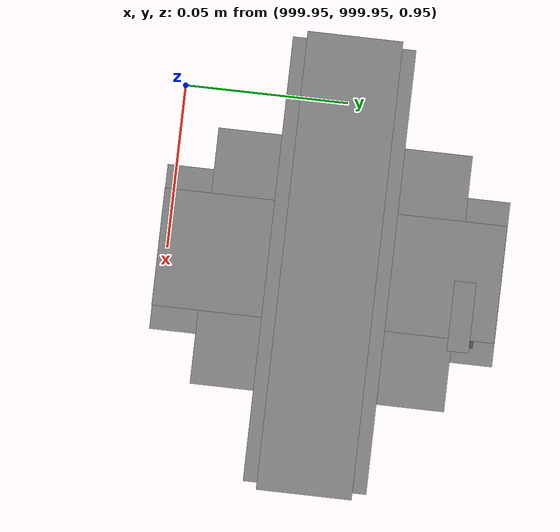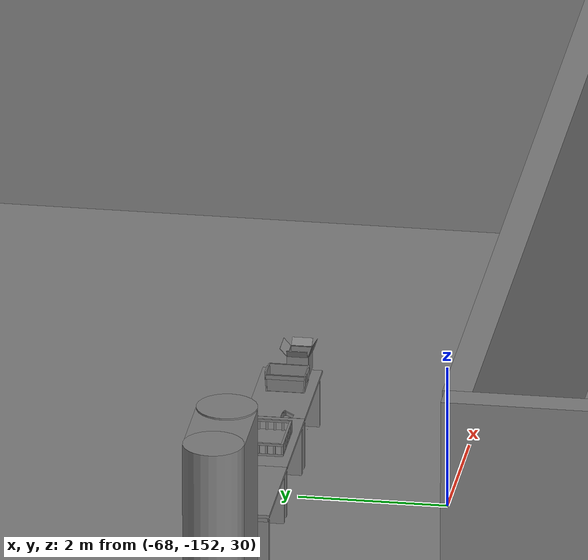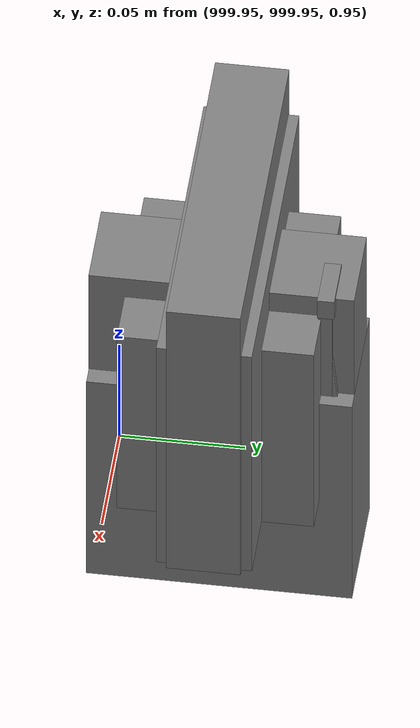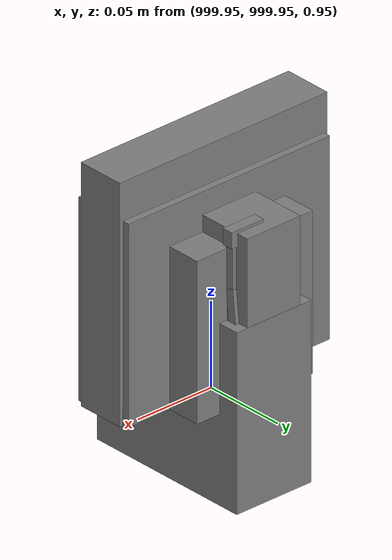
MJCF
<mujoco>
    <option gravity="0.000000000 0.000000000 -9.810000420" timestep="0.0049999999" integrator="implicitfast" density="1.225" viscosity="1.8000001e-05" noslip_iterations="10" iterations="100" sdf_iterations="50">
        <flag multiccd="disable"/>
    </option>
    <size memory="1000M"/>
    <compiler coordinate="local"/>
    <worldbody>
        <light cutoff="30" pos="0 1 1" dir="0 -1 -2"/>
        <light cutoff="30" pos="0 -1 1" dir="0 1 -2"/>
        <body pos="-64.866622925 -149.383972168 30.183746338" euler="89.999984741 89.999946594 0.000000000" name="openloong_gripper_2f85_fix_base_usda_bluebox_01">
            <geom contype="1" conaffinity="1" density="1000" type="box" material="" rgba="0.500000000 0.500000000 0.500000000 1.000000000" solimp="0.899999976 0.949999988 0.001000000" friction="1.000000000 0.005000000 0.000100000" solref="0.020000000 1.000000000" margin="0" condim="3" group="0" pos="0.276580811 0.187225342 0.000068665" quat="0.707106948 0.000077471 0.707106352 0.000077486" size="0.100000001 0.057999998 0.010000000" name="openloong_gripper_2f85_fix_base_usda_geom_DD444260_8CD6_4929_A577_DD065FA88FE6"/>
            <geom contype="1" conaffinity="1" density="1000" type="box" material="" rgba="0.500000000 0.500000000 0.500000000 1.000000000" solimp="0.899999976 0.949999988 0.001000000" friction="1.000000000 0.005000000 0.000100000" solref="0.020000000 1.000000000" margin="0" condim="3" group="0" pos="0.000000000 0.002883911 0.000000000" quat="0.999999881 0.000000000 0.000000000 0.000000000" size="0.254000008 0.003000000 0.172000006" name="openloong_gripper_2f85_fix_base_usda_geom_0F81B0B3_7611_4FF8_B203_757F3FF5858A"/>
            <geom contype="1" conaffinity="1" density="1000" type="box" material="" rgba="0.500000000 0.500000000 0.500000000 1.000000000" solimp="0.899999976 0.949999988 0.001000000" friction="1.000000000 0.005000000 0.000100000" solref="0.020000000 1.000000000" margin="0" condim="3" group="0" pos="0.000000000 0.124874115 0.173484802" quat="0.999796331 0.020176515 -0.000000015 0.000000030" size="0.259999990 0.119999997 0.007000000" name="openloong_gripper_2f85_fix_base_usda_geom_77AF4FC9_4C16_4361_BC47_64863BE77F9B"/>
            <geom contype="1" conaffinity="1" density="1000" type="box" material="" rgba="0.500000000 0.500000000 0.500000000 1.000000000" solimp="0.899999976 0.949999988 0.001000000" friction="1.000000000 0.005000000 0.000100000" solref="0.020000000 1.000000000" margin="0" condim="3" group="0" pos="0.000000000 0.124874115 -0.173469543" quat="0.999796331 -0.020176545 -0.000000015 0.000000000" size="0.259999990 0.119999997 0.007000000" name="openloong_gripper_2f85_fix_base_usda_geom_D0925476_279E_468D_B5D3_A2F52E32781B"/>
            <geom contype="1" conaffinity="1" density="1000" type="box" material="" rgba="0.500000000 0.500000000 0.500000000 1.000000000" solimp="0.899999976 0.949999988 0.001000000" friction="1.000000000 0.005000000 0.000100000" solref="0.020000000 1.000000000" margin="0" condim="3" group="0" pos="0.000000000 0.214008331 0.188980103" quat="0.999912977 0.013176724 0.000000015 0.000000000" size="0.259999990 0.029999999 0.012500000" name="openloong_gripper_2f85_fix_base_usda_geom_9EAD1F35_1450_4984_AD27_7EC5015AB999"/>
            <geom contype="1" conaffinity="1" density="1000" type="box" material="" rgba="0.500000000 0.500000000 0.500000000 1.000000000" solimp="0.899999976 0.949999988 0.001000000" friction="1.000000000 0.005000000 0.000100000" solref="0.020000000 1.000000000" margin="0" condim="3" group="0" pos="-0.258361816 0.125289917 0.001876831" quat="0.702796936 -0.020792112 0.710783124 0.020769298" size="0.189999998 0.119999997 0.009000000" name="openloong_gripper_2f85_fix_base_usda_geom_E086248D_B0B4_400F_A07C_C44D4BED1A35"/>
            <geom contype="1" conaffinity="1" density="1000" type="box" material="" rgba="0.500000000 0.500000000 0.500000000 1.000000000" solimp="0.899999976 0.949999988 0.001000000" friction="1.000000000 0.005000000 0.000100000" solref="0.020000000 1.000000000" margin="0" condim="3" group="0" pos="0.000000000 0.214008331 -0.188980103" quat="0.999912977 -0.013176769 0.000000030 0.000000015" size="0.259999990 0.029999999 0.012500000" name="openloong_gripper_2f85_fix_base_usda_geom_09263CEB_1509_43EE_924E_BACD4B2C50EA"/>
            <geom contype="1" conaffinity="1" density="1000" type="box" material="" rgba="0.500000000 0.500000000 0.500000000 1.000000000" solimp="0.899999976 0.949999988 0.001000000" friction="1.000000000 0.005000000 0.000100000" solref="0.020000000 1.000000000" margin="0" condim="3" group="0" pos="-0.276611328 0.187225342 0.000068665" quat="0.707106650 0.000077441 0.707106709 0.000077456" size="0.100000001 0.057999998 0.010000000" name="openloong_gripper_2f85_fix_base_usda_geom_675F421A_0E8C_4B85_BD13_E2570C39646B"/>
            <geom contype="1" conaffinity="1" density="1000" type="box" material="" rgba="0.500000000 0.500000000 0.500000000 1.000000000" solimp="0.899999976 0.949999988 0.001000000" friction="1.000000000 0.005000000 0.000100000" solref="0.020000000 1.000000000" margin="0" condim="3" group="0" pos="0.258331299 0.125289917 0.001876831" quat="0.702851415 0.018856421 0.710823774 -0.019329369" size="0.189999998 0.119999997 0.009000000" name="openloong_gripper_2f85_fix_base_usda_geom_5D8DEBCE_C166_4F26_BC84_6908743F4DDB"/>
            <freejoint name="openloong_gripper_2f85_fix_base_usda_bluebox_01_joint"/>
            <site size="0.005000000 0.005000000 0.005000000" rgba="0.500000000 0.500000000 0.500000000 1.000000000" pos="0.000000000 0.000000000 0.000000000" quat="0.999961913 0.008726534 0.000000000 0.000000000" group="0" type="sphere" name="openloong_gripper_2f85_fix_base_usda_bluebox_01site"/>
        </body>
        <body pos="-64.496299744 -149.491867065 30.235729218" euler="0.000000000 0.000000000 89.999946594" name="openloong_gripper_2f85_fix_base_usda_cardboardbox_01">
            <geom contype="1" conaffinity="1" density="1000" type="box" material="" rgba="0.500000000 0.500000000 0.500000000 1.000000000" solimp="0.899999976 0.949999988 0.001000000" friction="1.000000000 0.005000000 0.000100000" solref="0.020000000 1.000000000" margin="0" condim="3" group="0" pos="-0.003166199 -0.004086494 0.005052090" quat="1.000000000 0.000000000 0.000000000 0.000000000" size="0.142499998 0.177500010 0.005000000" name="openloong_gripper_2f85_fix_base_usda_geom_55360A01_70F7_4A0D_85A3_885EF6289C3A"/>
            <geom contype="1" conaffinity="1" density="1000" type="box" material="" rgba="0.500000000 0.500000000 0.500000000 1.000000000" solimp="0.899999976 0.949999988 0.001000000" friction="1.000000000 0.005000000 0.000100000" solref="0.020000000 1.000000000" margin="0" condim="3" group="0" pos="-0.003166199 0.170316696 0.150570869" quat="1.000000000 0.000000000 0.000000000 0.000000000" size="0.142499998 0.005000000 0.149999991" name="openloong_gripper_2f85_fix_base_usda_geom_54FFCEF2_54A1_4EDE_AA9D_23C413BAF13D"/>
            <geom contype="1" conaffinity="1" density="1000" type="box" material="" rgba="0.500000000 0.500000000 0.500000000 1.000000000" solimp="0.899999976 0.949999988 0.001000000" friction="1.000000000 0.005000000 0.000100000" solref="0.020000000 1.000000000" margin="0" condim="3" group="0" pos="-0.147399902 -0.005307198 0.150570869" quat="1.000000000 0.000000000 0.000000000 0.000000000" size="0.005000000 0.177500010 0.149999991" name="openloong_gripper_2f85_fix_base_usda_geom_455DF4DF_8348_476A_A30A_5697EBF580E1"/>
            <geom contype="1" conaffinity="1" density="1000" type="box" material="" rgba="0.500000000 0.500000000 0.500000000 1.000000000" solimp="0.899999976 0.949999988 0.001000000" friction="1.000000000 0.005000000 0.000100000" solref="0.020000000 1.000000000" margin="0" condim="3" group="0" pos="0.140275955 -0.005307198 0.150570869" quat="1.000000000 0.000000000 0.000000000 0.000000000" size="0.005000000 0.177500010 0.149999991" name="openloong_gripper_2f85_fix_base_usda_geom_6FE15C3E_E1FE_42B6_9D5F_3E4E739D7237"/>
            <geom contype="1" conaffinity="1" density="1000" type="box" material="" rgba="0.500000000 0.500000000 0.500000000 1.000000000" solimp="0.899999976 0.949999988 0.001000000" friction="1.000000000 0.005000000 0.000100000" solref="0.020000000 1.000000000" margin="0" condim="3" group="0" pos="-0.003166199 -0.181550980 0.150570869" quat="1.000000000 0.000000000 0.000000000 0.000000000" size="0.142499998 0.005000000 0.149999991" name="openloong_gripper_2f85_fix_base_usda_geom_F8675352_23B6_4B14_8231_5453AB53CFFE"/>
            <freejoint name="openloong_gripper_2f85_fix_base_usda_cardboardbox_01_joint"/>
            <site size="0.005000000 0.005000000 0.005000000" rgba="0.500000000 0.500000000 0.500000000 1.000000000" pos="0.000000000 0.000000000 0.000000000" quat="0.999961913 0.008726535 0.000000000 0.000000000" group="0" type="sphere" name="openloong_gripper_2f85_fix_base_usda_site_13524085_4031_4E7E_9947_3B2FAC3A6178"/>
            <body pos="0.139160156 -0.004048347 0.301930904" euler="-179.999954224 49.383502960 179.999954224" name="openloong_gripper_2f85_fix_base_usda_A1_006">
                <geom contype="1" conaffinity="1" density="1000" type="box" material="" rgba="0.500000000 0.500000000 0.500000000 1.000000000" solimp="0.899999976 0.949999988 0.001000000" friction="1.000000000 0.005000000 0.000100000" solref="0.020000000 1.000000000" margin="0" condim="3" group="0" pos="-0.071587563 0.000009537 0.001745224" quat="0.999999881 0.000000000 0.000000000 0.000000000" size="0.071249999 0.179999992 0.002500000" name="openloong_gripper_2f85_fix_base_usda_geom_6E33DCB0_8304_474F_ACBF_7F375454818A"/>
                <joint armature="0" stiffness="0.07" damping="0.0099999998" axis="0.000000 1.000000 0.000000" type="hinge" name="openloong_gripper_2f85_fix_base_usda_A1_006"/>
            </body>
            <body pos="-0.145902634 -0.004086494 0.301938057" euler="-180.000000000 -60.000011444 -180.000000000" name="openloong_gripper_2f85_fix_base_usda_A2_006">
                <geom contype="1" conaffinity="1" density="1000" type="box" material="" rgba="0.500000000 0.500000000 0.500000000 1.000000000" solimp="0.899999976 0.949999988 0.001000000" friction="1.000000000 0.005000000 0.000100000" solref="0.020000000 1.000000000" margin="0" condim="3" group="0" pos="0.071268082 0.000009537 0.002717972" quat="0.000002921 0.000000000 -0.000000030 0.999999881" size="0.071249999 0.179999992 0.002500000" name="openloong_gripper_2f85_fix_base_usda_geom_D862DED9_FCFD_4C11_B49F_68C6F2FE3EA9"/>
                <joint armature="0" stiffness="0.07" damping="0.0099999998" axis="0.000000 1.000000 0.000000" type="hinge" name="openloong_gripper_2f85_fix_base_usda_A2_006"/>
            </body>
            <body pos="-0.003385544 0.175991058 0.301930904" euler="-125.858116150 -0.000004561 0.000002331" name="openloong_gripper_2f85_fix_base_usda_B2_006">
                <geom contype="1" conaffinity="1" density="1000" type="box" material="" rgba="0.500000000 0.500000000 0.500000000 1.000000000" solimp="0.899999976 0.949999988 0.001000000" friction="1.000000000 0.005000000 0.000100000" solref="0.020000000 1.000000000" margin="0" condim="3" group="0" pos="0.000009537 -0.070939064 -0.002470016" quat="0.999614120 0.027776197 -0.000000015 0.000000030" size="0.137500003 0.064999998 0.005000000" name="openloong_gripper_2f85_fix_base_usda_geom_6091E607_EFD4_46A8_9681_4D63C171714C"/>
                <joint armature="0" stiffness="0.07" damping="0.0099999998" axis="1.000000 0.000000 0.000000" type="hinge" name="openloong_gripper_2f85_fix_base_usda_B2_006"/>
            </body>
            <body pos="-0.003385544 -0.184140205 0.301938057" euler="147.805557251 0.000000000 0.000000000" name="openloong_gripper_2f85_fix_base_usda_B1_006">
                <geom contype="1" conaffinity="1" density="1000" type="box" material="" rgba="0.500000000 0.500000000 0.500000000 1.000000000" solimp="0.899999976 0.949999988 0.001000000" friction="1.000000000 0.005000000 0.000100000" solref="0.020000000 1.000000000" margin="0" condim="3" group="0" pos="-0.000028610 0.070202351 -0.002703667" quat="0.999614179 -0.027776167 0.000000000 0.000000000" size="0.137500003 0.064999998 0.005000000" name="openloong_gripper_2f85_fix_base_usda_geom_17565FE9_D33E_4312_A608_47787EC2BB7D"/>
                <joint armature="0" stiffness="0.07" damping="0.0099999998" axis="1.000000 0.000000 0.000000" type="hinge" name="openloong_gripper_2f85_fix_base_usda_B1_006"/>
            </body>
        </body>
        <body pos="-65.882858276 -149.481979370 30.229999542" euler="-64.487716675 0.000000000 0.000000000" name="openloong_gripper_2f85_fix_base_usda_Barcode">
            <geom contype="1" conaffinity="1" density="1000" type="box" material="" rgba="0.500000000 0.500000000 0.500000000 1.000000000" solimp="0.899999976 0.949999988 0.001000000" friction="1.000000000 0.005000000 0.000100000" solref="0.020000000 1.000000000" margin="0" condim="3" group="0" pos="0.000000000 0.013038635 0.001419067" quat="0.000000000 0.000000000 0.000000000 1.000000119" size="0.034000002 0.010000000 0.017999999" name="openloong_gripper_2f85_fix_base_usda_geom_5F1D9ECB_5C09_4E22_A79A_CD799E109407"/>
            <geom contype="1" conaffinity="1" density="1000" type="box" material="" rgba="0.500000000 0.500000000 0.500000000 1.000000000" solimp="0.899999976 0.949999988 0.001000000" friction="1.000000000 0.005000000 0.000100000" solref="0.020000000 1.000000000" margin="0" condim="3" group="0" pos="0.000000000 -0.035301208 -0.007095337" quat="0.000000000 0.000000000 -0.043619365 0.999048233" size="0.028999999 0.010000000 0.020000000" name="openloong_gripper_2f85_fix_base_usda_geom_E1B8F210_80CA_4E17_B1B1_BC80388B3B2F"/>
            <geom contype="1" conaffinity="1" density="1000" type="box" material="" rgba="0.500000000 0.500000000 0.500000000 1.000000000" solimp="0.899999976 0.949999988 0.001000000" friction="1.000000000 0.005000000 0.000100000" solref="0.020000000 1.000000000" margin="0" condim="3" group="0" pos="0.000000000 -0.043411255 -0.011749268" quat="0.922262907 0.386563420 0.000000000 0.000000000" size="0.026000001 0.010000000 0.020000000" name="openloong_gripper_2f85_fix_base_usda_geom_B73BA454_8186_46BC_86BE_CB73C1C5F1DA"/>
            <geom contype="1" conaffinity="1" density="1000" type="box" material="" rgba="0.500000000 0.500000000 0.500000000 1.000000000" solimp="0.899999976 0.949999988 0.001000000" friction="1.000000000 0.005000000 0.000100000" solref="0.020000000 1.000000000" margin="0" condim="3" group="0" pos="0.000000000 -0.016967773 -0.031860352" quat="0.000000000 0.000000000 0.000000000 1.000000119" size="0.008000000 0.010000000 0.013000000" name="openloong_gripper_2f85_fix_base_usda_geom_CFB7D9BE_3DCB_4310_B99E_E47F96600C26"/>
            <geom contype="1" conaffinity="1" density="1000" type="box" material="" rgba="0.500000000 0.500000000 0.500000000 1.000000000" solimp="0.899999976 0.949999988 0.001000000" friction="1.000000000 0.005000000 0.000100000" solref="0.020000000 1.000000000" margin="0" condim="3" group="0" pos="0.000000000 -0.001869202 0.000312805" quat="0.953716993 0.300705761 0.000000000 0.000000000" size="0.032000002 0.010000000 0.018999999" name="openloong_gripper_2f85_fix_base_usda_geom_3E710345_8FDD_4251_BAE6_F24D992BDB47"/>
            <geom contype="1" conaffinity="1" density="1000" type="box" material="" rgba="0.500000000 0.500000000 0.500000000 1.000000000" solimp="0.899999976 0.949999988 0.001000000" friction="1.000000000 0.005000000 0.000100000" solref="0.020000000 1.000000000" margin="0" condim="3" group="0" pos="0.000000000 -0.019531250 -0.003173828" quat="0.953716993 0.300705761 0.000000000 0.000000000" size="0.030999999 0.010000000 0.020000000" name="openloong_gripper_2f85_fix_base_usda_geom_FD92D1F7_8389_4405_B4FF_59B589F5C41C"/>
            <geom contype="1" conaffinity="1" density="1000" type="box" material="" rgba="0.500000000 0.500000000 0.500000000 1.000000000" solimp="0.899999976 0.949999988 0.001000000" friction="1.000000000 0.005000000 0.000100000" solref="0.020000000 1.000000000" margin="0" condim="3" group="0" pos="0.000000000 -0.035301208 -0.007095337" quat="0.953716993 0.300705761 0.000000000 0.000000000" size="0.028999999 0.010000000 0.020000000" name="openloong_gripper_2f85_fix_base_usda_geom_57B446FA_CF57_4668_8E5C_0439FEA58428"/>
            <geom contype="1" conaffinity="1" density="1000" type="box" material="" rgba="0.500000000 0.500000000 0.500000000 1.000000000" solimp="0.899999976 0.949999988 0.001000000" friction="1.000000000 0.005000000 0.000100000" solref="0.020000000 1.000000000" margin="0" condim="3" group="0" pos="0.000000000 -0.042617798 -0.071121216" quat="0.000000000 0.000000000 0.000000000 1.000000119" size="0.013000000 0.021000000 0.059999999" name="openloong_gripper_2f85_fix_base_usda_geom_659B5EFB_BD7F_471B_BD67_C8CF429CD967"/>
            <freejoint name="openloong_gripper_2f85_fix_base_usda_Barcode_joint"/>
            <site size="0.005000000 0.005000000 0.005000000" rgba="0.500000000 0.500000000 0.500000000 1.000000000" pos="0.000000000 0.000000000 0.000000000" quat="1.000000000 0.000000000 0.000000000 0.000000000" group="0" type="sphere" name="openloong_gripper_2f85_fix_base_usda_Barcode_site"/>
        </body>
        <body pos="-66.745018005 -149.392349243 30.184000015" euler="0.000000000 0.000000000 89.999946594" name="[22332709622179]_Basket_01">
            <geom contype="1" conaffinity="1" density="1000" type="box" material="" rgba="0.500000000 0.500000000 0.500000000 1.000000000" solimp="0.899999976 0.949999988 0.001000000" friction="1.000000000 0.005000000 0.000100000" solref="0.020000000 1.000000000" margin="0" condim="3" group="0" pos="-0.052425385 0.389207840 0.089787483" quat="0.707107008 0.000000000 0.000000000 0.707106411" size="0.014249999 0.014249999 0.059999999" name="[22332709622179]_geom_C7B34887_B882_40D7_8054_907170C0F34A"/>
            <geom contype="1" conaffinity="1" density="1000" type="box" material="" rgba="0.500000000 0.500000000 0.500000000 1.000000000" solimp="0.899999976 0.949999988 0.001000000" friction="1.000000000 0.005000000 0.000100000" solref="0.020000000 1.000000000" margin="0" condim="3" group="0" pos="0.264015198 -0.133043289 0.089787483" quat="0.707107008 0.000000000 0.000000000 0.707106411" size="0.014249999 0.014249999 0.059999999" name="[22332709622179]_geom_140CF673_50E1_4F28_AECE_11D13F1D4C3A"/>
            <geom contype="1" conaffinity="1" density="1000" type="box" material="" rgba="0.500000000 0.500000000 0.500000000 1.000000000" solimp="0.899999976 0.949999988 0.001000000" friction="1.000000000 0.005000000 0.000100000" solref="0.020000000 1.000000000" margin="0" condim="3" group="0" pos="-0.264015198 -0.265548706 0.089793205" quat="0.707107008 0.000000000 0.000000000 0.707106411" size="0.014249999 0.014249999 0.059999999" name="[22332709622179]_geom_35806DEF_2D07_4462_91D2_BCD76384FEE7"/>
            <geom contype="1" conaffinity="1" density="1000" type="box" material="" rgba="0.500000000 0.500000000 0.500000000 1.000000000" solimp="0.899999976 0.949999988 0.001000000" friction="1.000000000 0.005000000 0.000100000" solref="0.020000000 1.000000000" margin="0" condim="3" group="0" pos="-0.160263062 -0.389322281 0.089793205" quat="0.707107008 0.000000000 0.000000000 0.707106411" size="0.014249999 0.014249999 0.059999999" name="[22332709622179]_geom_EDF19672_725F_4EDE_8E5A_096F9BC37157"/>
            <geom contype="1" conaffinity="1" density="1000" type="box" material="" rgba="0.500000000 0.500000000 0.500000000 1.000000000" solimp="0.899999976 0.949999988 0.001000000" friction="1.000000000 0.005000000 0.000100000" solref="0.020000000 1.000000000" margin="0" condim="3" group="0" pos="0.162265778 -0.389322281 0.089787483" quat="0.707107008 0.000000000 0.000000000 0.707106411" size="0.014249999 0.014249999 0.059999999" name="[22332709622179]_geom_9D24D8E7_3B05_4582_9250_2CEFB2A5ECDB"/>
            <geom contype="1" conaffinity="1" density="1000" type="box" material="" rgba="0.500000000 0.500000000 0.500000000 1.000000000" solimp="0.899999976 0.949999988 0.001000000" friction="1.000000000 0.005000000 0.000100000" solref="0.020000000 1.000000000" margin="0" condim="3" group="0" pos="0.264015198 0.389207840 0.089787483" quat="0.707107008 0.000000000 0.000000000 0.707106411" size="0.014249999 0.014249999 0.059999999" name="[22332709622179]_geom_D1AB4A4F_BDCF_4110_8A80_0565BA1776B6"/>
            <geom contype="1" conaffinity="1" density="1000" type="box" material="" rgba="0.500000000 0.500000000 0.500000000 1.000000000" solimp="0.899999976 0.949999988 0.001000000" friction="1.000000000 0.005000000 0.000100000" solref="0.020000000 1.000000000" margin="0" condim="3" group="0" pos="-0.264015198 -0.133043289 0.089793205" quat="0.707107008 0.000000000 0.000000000 0.707106411" size="0.014249999 0.014249999 0.059999999" name="[22332709622179]_geom_1C87095D_9D9C_4FF5_91BF_EAE2B5D2DE37"/>
            <geom contype="1" conaffinity="1" density="1000" type="box" material="" rgba="0.500000000 0.500000000 0.500000000 1.000000000" solimp="0.899999976 0.949999988 0.001000000" friction="1.000000000 0.005000000 0.000100000" solref="0.020000000 1.000000000" margin="0" condim="3" group="0" pos="-0.264026642 0.269256592 0.089793205" quat="0.707107008 0.000000000 0.000000000 0.707106411" size="0.014249999 0.014249999 0.059999999" name="[22332709622179]_geom_30C0DEA4_329B_4B71_849A_D24690BD966F"/>
            <geom contype="1" conaffinity="1" density="1000" type="box" material="" rgba="0.500000000 0.500000000 0.500000000 1.000000000" solimp="0.899999976 0.949999988 0.001000000" friction="1.000000000 0.005000000 0.000100000" solref="0.020000000 1.000000000" margin="0" condim="3" group="0" pos="0.054462433 0.389207840 0.089787483" quat="0.707107008 0.000000000 0.000000000 0.707106411" size="0.014249999 0.014249999 0.059999999" name="[22332709622179]_geom_9A7C2F27_F9A9_4239_A6B3_DF15547F6B87"/>
            <geom contype="1" conaffinity="1" density="1000" type="box" material="" rgba="0.500000000 0.500000000 0.500000000 1.000000000" solimp="0.899999976 0.949999988 0.001000000" friction="1.000000000 0.005000000 0.000100000" solref="0.020000000 1.000000000" margin="0" condim="3" group="0" pos="0.054462433 -0.389322281 0.089787483" quat="0.707107008 0.000000000 0.000000000 0.707106411" size="0.014249999 0.014249999 0.059999999" name="[22332709622179]_geom_2B88A38D_F384_472A_B01D_716CE566AFAA"/>
            <geom contype="1" conaffinity="1" density="1000" type="box" material="" rgba="0.500000000 0.500000000 0.500000000 1.000000000" solimp="0.899999976 0.949999988 0.001000000" friction="1.000000000 0.005000000 0.000100000" solref="0.020000000 1.000000000" margin="0" condim="3" group="0" pos="0.264015198 0.269256592 0.089793205" quat="0.707107008 0.000000000 0.000000000 0.707106411" size="0.014249999 0.014249999 0.059999999" name="[22332709622179]_geom_7CF90CB2_9536_4D1E_9082_A76C0E46F234"/>
            <geom contype="1" conaffinity="1" density="1000" type="box" material="" rgba="0.500000000 0.500000000 0.500000000 1.000000000" solimp="0.899999976 0.949999988 0.001000000" friction="1.000000000 0.005000000 0.000100000" solref="0.020000000 1.000000000" margin="0" condim="3" group="0" pos="0.264015198 -0.389322281 0.089787483" quat="0.707107008 0.000000000 0.000000000 0.707106411" size="0.014249999 0.014249999 0.059999999" name="[22332709622179]_geom_45AFAB5C_7F2E_45A3_945A_DEDC8F55795A"/>
            <geom contype="1" conaffinity="1" density="1000" type="box" material="" rgba="0.500000000 0.500000000 0.500000000 1.000000000" solimp="0.899999976 0.949999988 0.001000000" friction="1.000000000 0.005000000 0.000100000" solref="0.020000000 1.000000000" margin="0" condim="3" group="0" pos="0.000000000 0.000000000 0.015998840" quat="0.707107008 0.000000000 0.000000000 0.707106411" size="0.403499991 0.279000014 0.015750000" name="[22332709622179]_geom_CB0A2737_23A4_4BF8_B069_B862200826A9"/>
            <geom contype="1" conaffinity="1" density="1000" type="box" material="" rgba="0.500000000 0.500000000 0.500000000 1.000000000" solimp="0.899999976 0.949999988 0.001000000" friction="1.000000000 0.005000000 0.000100000" solref="0.020000000 1.000000000" margin="0" condim="3" group="0" pos="0.000000000 -0.389476776 0.163619041" quat="0.707107008 0.000000000 0.000000000 0.707106411" size="0.015000000 0.277500004 0.015750000" name="[22332709622179]_geom_F466C415_965B_4F8B_88B0_504084496244"/>
            <geom contype="1" conaffinity="1" density="1000" type="box" material="" rgba="0.500000000 0.500000000 0.500000000 1.000000000" solimp="0.899999976 0.949999988 0.001000000" friction="1.000000000 0.005000000 0.000100000" solref="0.020000000 1.000000000" margin="0" condim="3" group="0" pos="0.162265778 0.389207840 0.089787483" quat="0.707107008 0.000000000 0.000000000 0.707106411" size="0.014249999 0.014249999 0.059999999" name="[22332709622179]_geom_8610F4C3_AABE_46B8_BDE2_D8AFAEE88130"/>
            <geom contype="1" conaffinity="1" density="1000" type="box" material="" rgba="0.500000000 0.500000000 0.500000000 1.000000000" solimp="0.899999976 0.949999988 0.001000000" friction="1.000000000 0.005000000 0.000100000" solref="0.020000000 1.000000000" margin="0" condim="3" group="0" pos="0.000000000 0.389471054 0.163619041" quat="0.707107008 0.000000000 0.000000000 0.707106411" size="0.015000000 0.277500004 0.015750000" name="[22332709622179]_geom_F0255F9B_4EF7_4BFC_920E_A0C9B4994790"/>
            <geom contype="1" conaffinity="1" density="1000" type="box" material="" rgba="0.500000000 0.500000000 0.500000000 1.000000000" solimp="0.899999976 0.949999988 0.001000000" friction="1.000000000 0.005000000 0.000100000" solref="0.020000000 1.000000000" margin="0" condim="3" group="0" pos="-0.263511658 0.000000000 0.163619041" quat="0.707107008 0.000000000 0.000000000 0.707106411" size="0.403499991 0.015000000 0.015750000" name="[22332709622179]_geom_0AF08AC6_DA81_42C8_B2AC_1B94B91277AF"/>
            <geom contype="1" conaffinity="1" density="1000" type="box" material="" rgba="0.500000000 0.500000000 0.500000000 1.000000000" solimp="0.899999976 0.949999988 0.001000000" friction="1.000000000 0.005000000 0.000100000" solref="0.020000000 1.000000000" margin="0" condim="3" group="0" pos="-0.264015198 0.141334534 0.089793205" quat="0.707107008 0.000000000 0.000000000 0.707106411" size="0.014249999 0.014249999 0.059999999" name="[22332709622179]_geom_367C065D_2341_4C41_B688_04276EC4CB95"/>
            <geom contype="1" conaffinity="1" density="1000" type="box" material="" rgba="0.500000000 0.500000000 0.500000000 1.000000000" solimp="0.899999976 0.949999988 0.001000000" friction="1.000000000 0.005000000 0.000100000" solref="0.020000000 1.000000000" margin="0" condim="3" group="0" pos="0.264015198 -0.265548706 0.089787483" quat="0.707107008 0.000000000 0.000000000 0.707106411" size="0.014249999 0.014249999 0.059999999" name="[22332709622179]_geom_C85690E5_7FE4_4BB5_BDD2_15FBB763F9EE"/>
            <geom contype="1" conaffinity="1" density="1000" type="box" material="" rgba="0.500000000 0.500000000 0.500000000 1.000000000" solimp="0.899999976 0.949999988 0.001000000" friction="1.000000000 0.005000000 0.000100000" solref="0.020000000 1.000000000" margin="0" condim="3" group="0" pos="-0.160263062 0.389207840 0.089787483" quat="0.707107008 0.000000000 0.000000000 0.707106411" size="0.014249999 0.014249999 0.059999999" name="[22332709622179]_geom_49480621_535F_48C9_BB04_99E488E838FF"/>
            <geom contype="1" conaffinity="1" density="1000" type="box" material="" rgba="0.500000000 0.500000000 0.500000000 1.000000000" solimp="0.899999976 0.949999988 0.001000000" friction="1.000000000 0.005000000 0.000100000" solref="0.020000000 1.000000000" margin="0" condim="3" group="0" pos="-0.052425385 -0.389322281 0.089787483" quat="0.707107008 0.000000000 0.000000000 0.707106411" size="0.014249999 0.014249999 0.059999999" name="[22332709622179]_geom_45FEEE15_D03E_4D59_A6F3_736755D9FA48"/>
            <geom contype="1" conaffinity="1" density="1000" type="box" material="" rgba="0.500000000 0.500000000 0.500000000 1.000000000" solimp="0.899999976 0.949999988 0.001000000" friction="1.000000000 0.005000000 0.000100000" solref="0.020000000 1.000000000" margin="0" condim="3" group="0" pos="-0.264026642 -0.389322281 0.089793205" quat="0.707107008 0.000000000 0.000000000 0.707106411" size="0.014249999 0.014249999 0.059999999" name="[22332709622179]_geom_5B029720_1179_4234_A38F_22F85855B610"/>
            <geom contype="1" conaffinity="1" density="1000" type="box" material="" rgba="0.500000000 0.500000000 0.500000000 1.000000000" solimp="0.899999976 0.949999988 0.001000000" friction="1.000000000 0.005000000 0.000100000" solref="0.020000000 1.000000000" margin="0" condim="3" group="0" pos="0.264015198 0.141334534 0.089787483" quat="0.707107008 0.000000000 0.000000000 0.707106411" size="0.014249999 0.014249999 0.059999999" name="[22332709622179]_geom_25149ABF_63C9_493B_BBEC_C8754EC7ACAE"/>
            <geom contype="1" conaffinity="1" density="1000" type="box" material="" rgba="0.500000000 0.500000000 0.500000000 1.000000000" solimp="0.899999976 0.949999988 0.001000000" friction="1.000000000 0.005000000 0.000100000" solref="0.020000000 1.000000000" margin="0" condim="3" group="0" pos="-0.264015198 0.389207840 0.089793205" quat="0.707107008 0.000000000 0.000000000 0.707106411" size="0.014249999 0.014249999 0.059999999" name="[22332709622179]_geom_A6A3A1AB_7703_4849_96F6_B51E930C881B"/>
            <geom contype="1" conaffinity="1" density="1000" type="box" material="" rgba="0.500000000 0.500000000 0.500000000 1.000000000" solimp="0.899999976 0.949999988 0.001000000" friction="1.000000000 0.005000000 0.000100000" solref="0.020000000 1.000000000" margin="0" condim="3" group="0" pos="0.264015198 0.004480362 0.089787483" quat="0.707107008 0.000000000 0.000000000 0.707106411" size="0.014249999 0.014249999 0.059999999" name="[22332709622179]_geom_EDEC9AD4_20C2_4D64_9EC7_A0AEA2E3A2C6"/>
            <geom contype="1" conaffinity="1" density="1000" type="box" material="" rgba="0.500000000 0.500000000 0.500000000 1.000000000" solimp="0.899999976 0.949999988 0.001000000" friction="1.000000000 0.005000000 0.000100000" solref="0.020000000 1.000000000" margin="0" condim="3" group="0" pos="0.263694763 -0.000011444 0.163619041" quat="0.707107008 0.000000000 0.000000000 0.707106411" size="0.403499991 0.015000000 0.015750000" name="[22332709622179]_geom_1B6C237B_B62D_4BCF_869E_4C14626B0C91"/>
            <geom contype="1" conaffinity="1" density="1000" type="box" material="" rgba="0.500000000 0.500000000 0.500000000 1.000000000" solimp="0.899999976 0.949999988 0.001000000" friction="1.000000000 0.005000000 0.000100000" solref="0.020000000 1.000000000" margin="0" condim="3" group="0" pos="-0.264015198 0.004480362 0.089793205" quat="0.707107008 0.000000000 0.000000000 0.707106411" size="0.014249999 0.014249999 0.059999999" name="[22332709622179]_geom_A523A1A4_8F26_41E8_9491_59FD8C05E774"/>
            <freejoint name="[22332709622179]_joint_5CCDF753_080C_4FB6_8463_DDF77D2D71FB"/>
        </body>
        <body pos="0.000000000 0.000000000 0.000000000" euler="0.000000000 0.000000000 0.000000000" name="Static Objects_Static Objects">
            <geom contype="1" conaffinity="1" density="1000" type="box" material="" rgba="0.500000000 0.500000000 0.500000000 1.000000000" solimp="0.899999976 0.949999988 0.001000000" friction="1.000000000 0.005000000 0.000100000" solref="0.020000000 1.000000000" margin="0" condim="3" group="0" pos="-67.544113159 -149.365814209 29.727830887" quat="0.500000417 0.499999970 0.499999553 0.499999970" size="0.381000012 0.319999993 0.041000001" name="Static Objects_geom_BDD77057_91AC_4DDE_8872_6A910460C530"/>
            <geom contype="1" conaffinity="1" density="1000" type="box" material="" rgba="0.500000000 0.500000000 0.500000000 1.000000000" solimp="0.899999976 0.949999988 0.001000000" friction="1.000000000 0.005000000 0.000100000" solref="0.020000000 1.000000000" margin="0" condim="3" group="0" pos="-68.239501953 -149.365814209 30.086868286" quat="0.500000417 0.499999970 0.499999553 0.499999970" size="0.370999992 0.039500002 0.745000005" name="Static Objects_geom_0E937839_13A1_4520_9EEE_F32C08E6CE74"/>
            <geom contype="1" conaffinity="1" density="1000" type="box" material="" rgba="0.500000000 0.500000000 0.500000000 1.000000000" solimp="0.899999976 0.949999988 0.001000000" friction="1.000000000 0.005000000 0.000100000" solref="0.020000000 1.000000000" margin="0" condim="3" group="0" pos="-68.239501953 -149.365814209 30.147235870" quat="0.500000417 0.499999970 0.499999553 0.499999970" size="0.400000006 0.022000000 0.800000012" name="Static Objects_geom_FDB68260_3350_48AF_9180_77A50FC9968A"/>
            <geom contype="1" conaffinity="1" density="1000" type="box" material="" rgba="0.500000000 0.500000000 0.500000000 1.000000000" solimp="0.899999976 0.949999988 0.001000000" friction="1.000000000 0.005000000 0.000100000" solref="0.020000000 1.000000000" margin="0" condim="3" group="0" pos="-68.934890747 -149.365814209 29.727830887" quat="0.500000417 0.499999970 0.499999553 0.499999970" size="0.381000012 0.319999993 0.041000001" name="Static Objects_geom_B3B6BE73_7EFF_4882_BB34_F6B6A13130E8"/>
            <geom contype="1" conaffinity="1" density="1000" type="box" material="" rgba="0.500000000 0.500000000 0.500000000 1.000000000" solimp="0.899999976 0.949999988 0.001000000" friction="1.000000000 0.005000000 0.000100000" solref="0.020000000 1.000000000" margin="0" condim="3" group="0" pos="-68.239501953 -149.365814209 29.561563492" quat="0.500000417 0.499999970 0.499999553 0.499999970" size="0.020000000 0.022000000 0.660000026" name="Static Objects_geom_1A078FAB_36CD_4A26_BC91_86CFC3405521"/>
            <geom contype="1" conaffinity="1" density="1000" type="box" material="" rgba="0.500000000 0.500000000 0.500000000 1.000000000" solimp="0.899999976 0.949999988 0.001000000" friction="1.000000000 0.005000000 0.000100000" solref="0.020000000 1.000000000" margin="0" condim="3" group="0" pos="-65.945671082 -149.365814209 29.727830887" quat="0.500000417 0.499999970 0.499999553 0.499999970" size="0.381000012 0.319999993 0.041000001" name="Static Objects_geom_EA44CA06_9C3B_45AF_AB84_4506BA086B52"/>
            <geom contype="1" conaffinity="1" density="1000" type="box" material="" rgba="0.500000000 0.500000000 0.500000000 1.000000000" solimp="0.899999976 0.949999988 0.001000000" friction="1.000000000 0.005000000 0.000100000" solref="0.020000000 1.000000000" margin="0" condim="3" group="0" pos="-66.641059875 -149.365814209 30.086868286" quat="0.500000417 0.499999970 0.499999553 0.499999970" size="0.370999992 0.039500002 0.745000005" name="Static Objects_geom_E6D0A259_4D67_4457_BAFA_9D98BE18038C"/>
            <geom contype="1" conaffinity="1" density="1000" type="box" material="" rgba="0.500000000 0.500000000 0.500000000 1.000000000" solimp="0.899999976 0.949999988 0.001000000" friction="1.000000000 0.005000000 0.000100000" solref="0.020000000 1.000000000" margin="0" condim="3" group="0" pos="-66.641059875 -149.365814209 30.147235870" quat="0.500000417 0.499999970 0.499999553 0.499999970" size="0.400000006 0.022000000 0.800000012" name="Static Objects_geom_6C09A0DD_603A_4CBD_A5FD_F98666D7B857"/>
            <geom contype="1" conaffinity="1" density="1000" type="box" material="" rgba="0.500000000 0.500000000 0.500000000 1.000000000" solimp="0.899999976 0.949999988 0.001000000" friction="1.000000000 0.005000000 0.000100000" solref="0.020000000 1.000000000" margin="0" condim="3" group="0" pos="-67.336448669 -149.365814209 29.727830887" quat="0.500000417 0.499999970 0.499999553 0.499999970" size="0.381000012 0.319999993 0.041000001" name="Static Objects_geom_09CAFDCB_97F4_4297_ACDA_67204DA9E8C5"/>
            <geom contype="1" conaffinity="1" density="1000" type="box" material="" rgba="0.500000000 0.500000000 0.500000000 1.000000000" solimp="0.899999976 0.949999988 0.001000000" friction="1.000000000 0.005000000 0.000100000" solref="0.020000000 1.000000000" margin="0" condim="3" group="0" pos="-66.641059875 -149.365814209 29.561563492" quat="0.500000417 0.499999970 0.499999553 0.499999970" size="0.020000000 0.022000000 0.660000026" name="Static Objects_geom_64A66C96_0B8A_40FD_A7A3_B587DDA82D2C"/>
            <geom contype="1" conaffinity="1" density="1000" type="box" material="" rgba="0.500000000 0.500000000 0.500000000 1.000000000" solimp="0.899999976 0.949999988 0.001000000" friction="1.000000000 0.005000000 0.000100000" solref="0.020000000 1.000000000" margin="0" condim="3" group="0" pos="-64.338577271 -149.365814209 29.727830887" quat="0.500000417 0.499999970 0.499999553 0.499999970" size="0.381000012 0.319999993 0.041000001" name="Static Objects_geom_3196985F_A499_4808_B4AC_426D49D66D62"/>
            <geom contype="1" conaffinity="1" density="1000" type="box" material="" rgba="0.500000000 0.500000000 0.500000000 1.000000000" solimp="0.899999976 0.949999988 0.001000000" friction="1.000000000 0.005000000 0.000100000" solref="0.020000000 1.000000000" margin="0" condim="3" group="0" pos="-65.033966064 -149.365814209 30.086868286" quat="0.500000417 0.499999970 0.499999553 0.499999970" size="0.370999992 0.039500002 0.745000005" name="Static Objects_geom_49E22C5E_7AE7_4E5F_BA50_AEFC8965208C"/>
            <geom contype="1" conaffinity="1" density="1000" type="box" material="" rgba="0.500000000 0.500000000 0.500000000 1.000000000" solimp="0.899999976 0.949999988 0.001000000" friction="1.000000000 0.005000000 0.000100000" solref="0.020000000 1.000000000" margin="0" condim="3" group="0" pos="-65.033966064 -149.365814209 30.147235870" quat="0.500000417 0.499999970 0.499999553 0.499999970" size="0.400000006 0.022000000 0.800000012" name="Static Objects_geom_B2B17F7C_AD0A_4E3F_9A6A_E901D724BDCC"/>
            <geom contype="1" conaffinity="1" density="1000" type="box" material="" rgba="0.500000000 0.500000000 0.500000000 1.000000000" solimp="0.899999976 0.949999988 0.001000000" friction="1.000000000 0.005000000 0.000100000" solref="0.020000000 1.000000000" margin="0" condim="3" group="0" pos="-65.729354858 -149.365814209 29.727830887" quat="0.500000417 0.499999970 0.499999553 0.499999970" size="0.381000012 0.319999993 0.041000001" name="Static Objects_geom_061611E7_4E07_4413_AAF1_02C56C9FDA36"/>
            <geom contype="1" conaffinity="1" density="1000" type="box" material="" rgba="0.500000000 0.500000000 0.500000000 1.000000000" solimp="0.899999976 0.949999988 0.001000000" friction="1.000000000 0.005000000 0.000100000" solref="0.020000000 1.000000000" margin="0" condim="3" group="0" pos="-65.033966064 -149.365814209 29.561563492" quat="0.500000417 0.499999970 0.499999553 0.499999970" size="0.020000000 0.022000000 0.660000026" name="Static Objects_geom_E3ECDE38_5E96_4897_9FB3_D00270271230"/>
            <geom contype="1" conaffinity="1" density="1000" type="box" material="" rgba="0.500000000 0.500000000 0.500000000 1.000000000" solimp="0.899999976 0.949999988 0.001000000" friction="1.000000000 0.005000000 0.000100000" solref="0.020000000 1.000000000" margin="0" condim="3" group="0" pos="-61.754566193 -137.853729248 33.906845093" quat="0.707107067 0.000000000 0.000000000 0.707106471" size="0.759999990 0.759999990 4.500000000" name="Static Objects_geom_352BCBEA_190F_40BD_BEA1_E00D1CD175C1"/>
            <geom contype="1" conaffinity="1" density="1000" type="box" material="" rgba="0.500000000 0.500000000 0.500000000 1.000000000" solimp="0.899999976 0.949999988 0.001000000" friction="1.000000000 0.005000000 0.000100000" solref="0.020000000 1.000000000" margin="0" condim="3" group="0" pos="-57.511135101 -144.927108765 31.707921982" quat="1.000000000 0.000000000 0.000000000 0.000000000" size="0.200000003 8.000000000 2.299999952" name="Static Objects_geom_CDCEF65F_2319_43A8_905C_EE79E4FE306A"/>
            <geom contype="1" conaffinity="1" density="1000" type="box" material="" rgba="0.500000000 0.500000000 0.500000000 1.000000000" solimp="0.899999976 0.949999988 0.001000000" friction="1.000000000 0.005000000 0.000100000" solref="0.020000000 1.000000000" margin="0" condim="3" group="0" pos="-80.517646790 -157.574050903 31.688196182" quat="0.707107067 0.000000000 0.000000000 0.707106471" size="0.600000024 0.600000024 2.299999952" name="Static Objects_geom_B23F288D_660D_4C06_A86A_B29575E03A72"/>
            <geom contype="1" conaffinity="1" density="1000" type="box" material="" rgba="0.500000000 0.500000000 0.500000000 1.000000000" solimp="0.899999976 0.949999988 0.001000000" friction="1.000000000 0.005000000 0.000100000" solref="0.020000000 1.000000000" margin="0" condim="3" group="0" pos="-80.711044312 -147.414932251 31.666158676" quat="1.000000000 0.000000000 0.000000000 0.000000000" size="0.200000003 10.000000000 2.299999952" name="Static Objects_geom_6AFFE43F_ADD2_4C7E_893B_A2B705F4A9FE"/>
            <geom contype="1" conaffinity="1" density="1000" type="box" material="" rgba="0.500000000 0.500000000 0.500000000 1.000000000" solimp="0.899999976 0.949999988 0.001000000" friction="1.000000000 0.005000000 0.000100000" solref="0.020000000 1.000000000" margin="0" condim="3" group="0" pos="-57.687217712 -137.434692383 31.688196182" quat="0.707107067 0.000000000 0.000000000 0.707106471" size="0.600000024 0.600000024 2.299999952" name="Static Objects_geom_0F3890D9_A6AC_404F_80F2_2D964012AD05"/>
            <geom contype="1" conaffinity="1" density="1000" type="box" material="" rgba="0.500000000 0.500000000 0.500000000 1.000000000" solimp="0.899999976 0.949999988 0.001000000" friction="1.000000000 0.005000000 0.000100000" solref="0.020000000 1.000000000" margin="0" condim="3" group="0" pos="-69.537033081 -140.263229370 31.714921951" quat="0.707107067 0.000000000 0.000000000 0.707106471" size="0.759999990 4.500000000 2.299999952" name="Static Objects_geom_B947AA9C_AB66_48EF_AA96_F42ED53F4B85"/>
            <geom contype="1" conaffinity="1" density="1000" type="box" material="" rgba="0.500000000 0.500000000 0.500000000 1.000000000" solimp="0.899999976 0.949999988 0.001000000" friction="1.000000000 0.005000000 0.000100000" solref="0.020000000 1.000000000" margin="0" condim="3" group="0" pos="-80.073638916 -137.853713989 33.906845093" quat="0.707107067 0.000000000 0.000000000 0.707106471" size="0.759999990 0.759999990 4.500000000" name="Static Objects_geom_B86E8A2C_1E92_4E0D_BE58_C34C5A360396"/>
            <geom contype="1" conaffinity="1" density="1000" type="box" material="" rgba="0.500000000 0.500000000 0.500000000 1.000000000" solimp="0.899999976 0.949999988 0.001000000" friction="1.000000000 0.005000000 0.000100000" solref="0.020000000 1.000000000" margin="0" condim="3" group="0" pos="-73.406707764 -155.734664917 31.707921982" quat="1.000000000 0.000000000 0.000000000 0.000000000" size="0.200000003 3.000000000 2.299999952" name="Static Objects_geom_58C79990_C2E2_47E6_A2B4_D3ABFB361634"/>
            <geom contype="1" conaffinity="1" density="1000" type="box" material="" rgba="0.500000000 0.500000000 0.500000000 1.000000000" solimp="0.899999976 0.949999988 0.001000000" friction="1.000000000 0.005000000 0.000100000" solref="0.020000000 1.000000000" margin="0" condim="3" group="0" pos="-68.497543335 -137.448257446 31.707921982" quat="0.707107067 0.000000000 0.000000000 0.707106471" size="0.200000003 14.000000000 2.299999952" name="Static Objects_geom_00F6ABF3_A025_44B9_8FDD_A4CCB5362FAB"/>
            <geom contype="1" conaffinity="1" density="1000" type="cylinder" material="" rgba="0.500000000 0.500000000 0.500000000 1.000000000" solimp="0.899999976 0.949999988 0.001000000" friction="1.000000000 0.005000000 0.000100000" solref="0.020000000 1.000000000" margin="0" condim="3" group="0" pos="-68.868522644 -142.134506226 31.711090088" quat="0.707107067 0.000000000 0.000000000 0.707106471" size="0.509999990 2.299999952 1.000000000" name="Static Objects_geom_8406170A_C495_4A47_8A7C_608C09D1C283"/>
            <geom contype="1" conaffinity="1" density="1000" type="plane" material="" rgba="0.500000000 0.500000000 0.500000000 1.000000000" solimp="0.899999976 0.949999988 0.001000000" friction="1.000000000 0.005000000 0.000100000" solref="0.020000000 1.000000000" margin="0" condim="3" group="0" pos="-72.873703003 -147.131927490 29.409669876" quat="1.000000000 0.000000000 0.000000000 0.000000000" size="18.000000000 14.000000000 1.000000000" name="Static Objects_geom_DB5505C2_4368_4ADE_9762_8092EA59846C"/>
            <geom contype="1" conaffinity="1" density="1000" type="box" material="" rgba="0.500000000 0.500000000 0.500000000 1.000000000" solimp="0.899999976 0.949999988 0.001000000" friction="1.000000000 0.005000000 0.000100000" solref="0.020000000 1.000000000" margin="0" condim="3" group="0" pos="-79.943580627 -157.782272339 31.707921982" quat="0.707107067 0.000000000 0.000000000 0.707106471" size="0.200000003 7.000000000 2.299999952" name="Static Objects_geom_A76D62EC_2316_41BB_853C_DF1F1ED52D88"/>
            <geom contype="1" conaffinity="1" density="1000" type="box" material="" rgba="0.500000000 0.500000000 0.500000000 1.000000000" solimp="0.899999976 0.949999988 0.001000000" friction="1.000000000 0.005000000 0.000100000" solref="0.020000000 1.000000000" margin="0" condim="3" group="0" pos="-65.421028137 -152.903442383 31.707921982" quat="0.707107067 0.000000000 0.000000000 0.707106471" size="0.200000003 7.800000191 2.299999952" name="Static Objects_geom_D100E712_29BF_4F95_8EBE_03C65185A010"/>
            <geom contype="1" conaffinity="1" density="1000" type="box" material="" rgba="0.500000000 0.500000000 0.500000000 1.000000000" solimp="0.899999976 0.949999988 0.001000000" friction="1.000000000 0.005000000 0.000100000" solref="0.020000000 1.000000000" margin="0" condim="3" group="0" pos="-74.776908875 -149.964416504 31.688196182" quat="1.000000000 0.000000000 0.000000000 0.000000000" size="0.600000024 0.409999996 2.299999952" name="Static Objects_geom_9623BA22_AAF5_4A9E_865F_9A675215331C"/>
            <geom contype="1" conaffinity="1" density="1000" type="cylinder" material="" rgba="0.500000000 0.500000000 0.500000000 1.000000000" solimp="0.899999976 0.949999988 0.001000000" friction="1.000000000 0.005000000 0.000100000" solref="0.020000000 1.000000000" margin="0" condim="3" group="0" pos="-60.161884308 -142.134506226 31.711090088" quat="0.707107067 0.000000000 0.000000000 0.707106471" size="0.509999990 2.299999952 1.000000000" name="Static Objects_geom_B7C58BF3_558B_4D80_B709_4F9C2B82FC6F"/>
            <geom contype="1" conaffinity="1" density="1000" type="cylinder" material="" rgba="0.500000000 0.500000000 0.500000000 1.000000000" solimp="0.899999976 0.949999988 0.001000000" friction="1.000000000 0.005000000 0.000100000" solref="0.020000000 1.000000000" margin="0" condim="3" group="0" pos="-75.382453918 -149.963455200 31.711090088" quat="0.707107067 0.000000000 0.000000000 0.707106471" size="0.409999996 2.299999952 1.000000000" name="Static Objects_geom_F35386F6_E1D7_42EA_A461_C3E006503405"/>
            <geom contype="1" conaffinity="1" density="1000" type="cylinder" material="" rgba="0.500000000 0.500000000 0.500000000 1.000000000" solimp="0.899999976 0.949999988 0.001000000" friction="1.000000000 0.005000000 0.000100000" solref="0.020000000 1.000000000" margin="0" condim="3" group="0" pos="-74.154960632 -149.963455200 31.711090088" quat="0.707107067 0.000000000 0.000000000 0.707106471" size="0.409999996 2.299999952 1.000000000" name="Static Objects_geom_D78B0D72_04F6_419C_A0A6_DE98F09DC4F7"/>
            <geom contype="1" conaffinity="1" density="1000" type="cylinder" material="" rgba="0.500000000 0.500000000 0.500000000 1.000000000" solimp="0.899999976 0.949999988 0.001000000" friction="1.000000000 0.005000000 0.000100000" solref="0.020000000 1.000000000" margin="0" condim="3" group="0" pos="-77.566612244 -142.134506226 31.711090088" quat="0.707107067 0.000000000 0.000000000 0.707106471" size="0.509999990 2.299999952 1.000000000" name="Static Objects_geom_0B0E7205_1936_43E8_B097_3FA592F4205D"/>
        </body>
        <body pos="-66.174499512 -149.095001221 31.170047760" euler="154.001296997 61.710510254 165.185623169" mocap="true" name="spotlight2_SpotLight"/>
        <body pos="1000.000000000 999.999938965 1.000000000" euler="0.000000000 0.000000000 180.000000000" name="openloong_gripper_2f85_fix_base_usda_intelcore_i5">
            <geom contype="1" conaffinity="1" density="1000" type="box" material="" rgba="0.500000000 0.500000000 0.500000000 1.000000000" solimp="0.899999976 0.949999988 0.001000000" friction="1.000000000 0.005000000 0.000100000" solref="0.020000000 1.000000000" margin="0" condim="3" group="0" pos="0.000000000 0.000000000 0.051722717" quat="0.707106709 0.000000000 0.000000000 -0.707106769" size="0.052800000 0.018080002 0.052800000" name="openloong_gripper_2f85_fix_base_usda_geom_09D91524_759D_46EA_88D3_8AA132D23B9C"/>
            <freejoint name="openloong_gripper_2f85_fix_base_usda_intelcore_i5_joint"/>
            <site size="0.005000000 0.005000000 0.005000000" rgba="0.500000000 0.500000000 0.500000000 1.000000000" pos="0.000000000 0.000000000 0.000000000" quat="0.999961913 0.008726534 0.000000000 0.000000000" group="0" type="sphere" name="openloong_gripper_2f85_fix_base_usda_intelcore_i5site"/>
        </body>
        <body pos="1000.000000000 1000.000000000 1.000000000" euler="0.000011953 0.000005123 -179.999984741" name="openloong_gripper_2f85_fix_base_usda_intel_box">
            <geom contype="1" conaffinity="1" density="1000" type="box" material="" rgba="0.500000000 0.500000000 0.500000000 1.000000000" solimp="0.899999976 0.949999988 0.001000000" friction="1.000000000 0.005000000 0.000100000" solref="0.020000000 1.000000000" margin="0" condim="3" group="0" pos="0.000000000 -0.000067139 0.000082284" quat="0.707106709 0.000000225 0.000000253 0.707106650" size="0.052800003 0.025300000 0.052800003" name="openloong_gripper_2f85_fix_base_usda_geom_65D9050E_5029_4ABF_AEE6_84D7FC539F17"/>
            <freejoint name="openloong_gripper_2f85_fix_base_usda_intel_box_joint"/>
            <site size="0.005000000 0.005000000 0.005000000" rgba="0.500000000 0.500000000 0.500000000 1.000000000" pos="0.000000000 0.000000000 0.000000000" quat="0.999961913 0.008726500 0.000000000 0.000000000" group="0" type="sphere" name="openloong_gripper_2f85_fix_base_usda_intel_boxsite"/>
        </body>
        <body pos="-66.033370972 -149.017700195 31.169290543" euler="166.179977417 -57.538581848 -119.643951416" mocap="true" name="spotlight6_SpotLight"/>
        <body pos="1000.000000000 1000.000000000 1.000000000" euler="0.000000000 0.000000000 180.000000000" name="openloong_gripper_2f85_fix_base_usda_wifi_box">
            <geom contype="1" conaffinity="1" density="1000" type="box" material="" rgba="0.500000000 0.500000000 0.500000000 1.000000000" solimp="0.899999976 0.949999988 0.001000000" friction="1.000000000 0.005000000 0.000100000" solref="0.020000000 1.000000000" margin="0" condim="3" group="0" pos="0.000000000 0.000000000 0.058978677" quat="0.000000000 0.000000047 0.000000000 1.000000000" size="0.068499997 0.018999999 0.059000000" name="openloong_gripper_2f85_fix_base_usda_geom_9B5BB645_6CDF_472C_8276_22F6CA4D6A41"/>
            <freejoint name="openloong_gripper_2f85_fix_base_usda_wifi_box_joint"/>
            <site size="0.005000000 0.005000000 0.005000000" rgba="0.500000000 0.500000000 0.500000000 1.000000000" pos="0.000000000 0.000000000 0.000000000" quat="0.999961913 0.008726500 0.000000000 0.000000000" group="0" type="sphere" name="openloong_gripper_2f85_fix_base_usda_wifi_boxsite"/>
        </body>
        <body pos="1000.000000000 1000.000000000 1.000000000" euler="0.000000000 0.000000000 180.000000000" name="openloong_gripper_2f85_fix_base_usda_cpu_fan">
            <geom contype="1" conaffinity="1" density="1000" type="box" material="" rgba="0.500000000 0.500000000 0.500000000 1.000000000" solimp="0.899999976 0.949999988 0.001000000" friction="1.000000000 0.005000000 0.000100000" solref="0.020000000 1.000000000" margin="0" condim="3" group="0" pos="0.000000000 0.000000000 0.070034981" quat="0.000000000 0.000000000 0.000000000 1.000000000" size="0.070700005 0.014699999 0.070700005" name="openloong_gripper_2f85_fix_base_usda_geom_91DFF095_9D84_4D73_B3F2_7D707BE65FB9"/>
            <freejoint name="openloong_gripper_2f85_fix_base_usda_cpu_fan_joint"/>
            <site size="0.005000000 0.005000000 0.005000000" rgba="0.500000000 0.500000000 0.500000000 1.000000000" pos="0.000000000 0.000000000 0.000000000" quat="0.999961913 0.008726535 0.000000000 0.000000000" group="0" type="sphere" name="openloong_gripper_2f85_fix_base_usda_cpu_fancsite"/>
        </body>
        <body pos="1000.000000000 1000.000000000 1.000000000" euler="0.000000000 0.000000000 180.000000000" name="openloong_gripper_2f85_fix_base_usda_battery_01">
            <geom contype="1" conaffinity="1" density="1000" type="box" material="" rgba="0.500000000 0.500000000 0.500000000 1.000000000" solimp="0.899999976 0.949999988 0.001000000" friction="1.000000000 0.005000000 0.000100000" solref="0.020000000 1.000000000" margin="0" condim="3" group="0" pos="-0.011123657 -0.041940309 0.101691343" quat="1.000000000 0.000000000 0.000000000 0.000000000" size="0.010800000 0.003375000 0.004725000" name="openloong_gripper_2f85_fix_base_usda_geom_0D7ACD8C_A5E9_4D07_BD1C_3808F7010598"/>
            <geom contype="1" conaffinity="1" density="1000" type="box" material="" rgba="0.500000000 0.500000000 0.500000000 1.000000000" solimp="0.899999976 0.949999988 0.001000000" friction="1.000000000 0.005000000 0.000100000" solref="0.020000000 1.000000000" margin="0" condim="3" group="0" pos="-0.010876465 -0.044247437 0.047066893" quat="0.998702705 -0.050920475 0.000000000 0.000000000" size="0.009450001 0.002700000 0.024975000" name="openloong_gripper_2f85_fix_base_usda_geom_AFC00BB6_88F3_4A32_A9EA_659C835B6087"/>
            <geom contype="1" conaffinity="1" density="1000" type="box" material="" rgba="0.500000000 0.500000000 0.500000000 1.000000000" solimp="0.899999976 0.949999988 0.001000000" friction="1.000000000 0.005000000 0.000100000" solref="0.020000000 1.000000000" margin="0" condim="3" group="0" pos="-0.001235962 -0.000659180 0.047381196" quat="1.000000000 0.000000000 0.000000000 0.000000000" size="0.039420001 0.039150000 0.047250003" name="openloong_gripper_2f85_fix_base_usda_geom_5C8A832A_1C37_4686_9591_14EC800E4C5F"/>
            <geom contype="1" conaffinity="1" density="1000" type="box" material="" rgba="0.500000000 0.500000000 0.500000000 1.000000000" solimp="0.899999976 0.949999988 0.001000000" friction="1.000000000 0.005000000 0.000100000" solref="0.020000000 1.000000000" margin="0" condim="3" group="0" pos="-0.010876465 -0.039138794 0.009851727" quat="1.000000000 0.000000000 0.000000000 0.000000000" size="0.009450001 0.010800000 0.013500000" name="openloong_gripper_2f85_fix_base_usda_geom_B1AF6BCD_59DE_4541_9D42_C5A6C4CE92F2"/>
            <geom contype="1" conaffinity="1" density="1000" type="box" material="" rgba="0.500000000 0.500000000 0.500000000 1.000000000" solimp="0.899999976 0.949999988 0.001000000" friction="1.000000000 0.005000000 0.000100000" solref="0.020000000 1.000000000" margin="0" condim="3" group="0" pos="-0.010876465 -0.041528322 0.071508206" quat="1.000000000 0.000000000 0.000000000 0.000000000" size="0.009450001 0.002700000 0.027000001" name="openloong_gripper_2f85_fix_base_usda_geom_F884EB33_29E4_4869_9F49_3B3860156A87"/>
            <freejoint name="openloong_gripper_2f85_fix_base_usda_battery_01_joint"/>
            <site size="0.005000000 0.005000000 0.005000000" rgba="0.500000000 0.500000000 0.500000000 1.000000000" pos="0.000000000 0.000000000 0.000000000" quat="0.999961913 0.008726500 0.000000000 0.000000000" group="0" type="sphere" name="openloong_gripper_2f85_fix_base_usda_battery_01site"/>
        </body>
        <body pos="-66.308288574 -149.408828735 31.165628433" euler="-12.972414017 46.660171509 -175.798934937" mocap="true" name="spotlight4_SpotLight"/>
        <body pos="-66.291030884 -149.869689941 29.018842697" euler="0.000000000 0.000000000 89.999946594" mocap="true" name="openloong_gripper_2f85_fix_base_usda_leftHandMocap"/>
        <body pos="-66.291030884 -149.869689941 29.018842697" euler="0.000000000 0.000000000 89.999946594" mocap="true" name="openloong_gripper_2f85_fix_base_usda_rightHandMocap"/>
        <body pos="-66.291030884 -149.869689941 30.218843460" euler="0.000000000 0.000000000 89.999946594" name="openloong_gripper_2f85_fix_base_usda_base_link">
            <geom contype="1" conaffinity="1" density="1000" type="mesh" material="" rgba="0.783999979 0.783999979 0.783999979 1.000000000" solimp="0.899999976 0.949999988 0.001000000" friction="1.000000000 0.005000000 0.000100000" solref="0.020000000 1.000000000" margin="0" condim="3" group="3" mesh="base_link" pos="0.000000000 0.000000000 0.000000000" quat="1.000000000 0.000000000 0.000000000 0.000000000" size="1.000000000 1.000000000 1.000000000" name="openloong_gripper_2f85_fix_base_usda__geom_7_2BE3D8B5_EC63_46EB_9082_4C6C8645514B"/>
            <site size="0.005000000 0.005000000 0.005000000" rgba="0.500000000 0.500000000 0.500000000 1.000000000" pos="0.000000000 0.000000000 0.000000000" quat="1.000000000 0.000000000 0.000000000 0.000000000" group="0" type="sphere" name="openloong_gripper_2f85_fix_base_usda_imu"/>
            <inertial mass="22.447001" pos="-0.005664100 -0.001336700 0.238289997" diaginertia="0.374352545 0.277180195 0.220617250" quat="0.999247074 0.035235517 -0.015086859 0.006023135"/>
            <body pos="0.000000000 0.000000000 0.299997330" euler="0.000000000 0.000000000 0.000000000" name="openloong_gripper_2f85_fix_base_usda_dummy_body">
                <geom contype="1" conaffinity="1" density="1000" type="sphere" material="" rgba="0.783999979 0.783999979 0.783999979 1.000000000" solimp="0.899999976 0.949999988 0.001000000" friction="1.000000000 0.005000000 0.000100000" solref="0.020000000 1.000000000" margin="0" condim="3" group="3" pos="0.000000000 0.000000000 0.000000000" quat="1.000000000 0.000000000 0.000000000 0.000000000" size="0.010000000 0.000000000 0.000000000" name="openloong_gripper_2f85_fix_base_usda__geom_8_A79D61D1_C33D_4FBC_9CA2_1D2651C5A921"/>
                <joint armature="0.0099999998" stiffness="0" damping="0.1" axis="0.000000 0.000000 1.000000" type="hinge" name="openloong_gripper_2f85_fix_base_usda_dummy_joint"/>
                <site size="0.010000000 0.005000000 0.005000000" rgba="0.500000000 0.500000000 0.500000000 1.000000000" pos="0.000000000 0.000000000 0.000000000" quat="1.000000000 0.000000000 0.000000000 0.000000000" group="3" type="sphere" name="openloong_gripper_2f85_fix_base_usda_dummy_site"/>
            </body>
            <body pos="0.009002686 0.000000000 0.406400681" euler="0.000000000 0.000000000 0.000000000" name="openloong_gripper_2f85_fix_base_usda_Link_head_yaw">
                <geom contype="1" conaffinity="1" density="1000" type="mesh" material="" rgba="0.783999979 0.783999979 0.783999979 1.000000000" solimp="0.899999976 0.949999988 0.001000000" friction="1.000000000 0.005000000 0.000100000" solref="0.020000000 1.000000000" margin="0" condim="3" group="3" mesh="Link_head_yaw" pos="0.000000000 0.000000000 0.000000000" quat="1.000000000 0.000000000 0.000000000 0.000000000" size="1.000000000 1.000000000 1.000000000" name="openloong_gripper_2f85_fix_base_usda__geom_10_0D466363_2C5D_41FD_9604_F515756EDFB0"/>
                <inertial mass="0.84249002" pos="0.000000000 -0.002081400 0.044801001" diaginertia="0.000700588 0.000629000 0.000553812" quat="0.706933022 -0.015675601 0.015677100 0.706933022"/>
                <body pos="0.000000000 -0.034599304 0.048500061" euler="0.000000000 0.000000000 0.000000000" name="openloong_gripper_2f85_fix_base_usda_Link_head_pitch">
                    <geom contype="1" conaffinity="1" density="1000" type="mesh" material="" rgba="0.783999979 0.783999979 0.783999979 1.000000000" solimp="0.899999976 0.949999988 0.001000000" friction="1.000000000 0.005000000 0.000100000" solref="0.020000000 1.000000000" margin="0" condim="3" group="3" mesh="Link_head_pitch" pos="0.000000000 0.000000000 0.000000000" quat="1.000000000 0.000000000 0.000000000 0.000000000" size="1.000000000 1.000000000 1.000000000" name="openloong_gripper_2f85_fix_base_usda__geom_12_EF01B867_A79F_4B95_BBBD_B023576CB363"/>
                    <inertial mass="1.3943" pos="0.020569000 0.033004001 0.125000000" diaginertia="0.006381400 0.006289940 0.004481460" quat="0.973390222 0.008406822 0.228157058 0.019624906"/>
                    <body pos="0.000000000 0.029998779 0.000000000" euler="0.000000000 0.000000000 0.000000000" name="openloong_gripper_2f85_fix_base_usda_neck_center_body">
                        <site size="0.010000000 0.005000000 0.005000000" rgba="0.500000000 0.500000000 0.500000000 1.000000000" pos="0.000000000 0.000000000 0.000000000" quat="1.000000000 0.000000000 0.000000000 0.000000000" group="3" type="sphere" name="openloong_gripper_2f85_fix_base_usda_neck_center_site"/>
                        <body pos="0.020004272 0.000000000 0.149999619" euler="-0.000002229 39.998176575 -90.000205994" name="openloong_gripper_2f85_fix_base_usda_camera_head">
                            <site size="0.010000000 0.005000000 0.005000000" rgba="0.500000000 0.500000000 0.500000000 1.000000000" pos="0.000000000 0.000000000 0.000000000" quat="1.000000000 0.000000000 0.000000000 0.000000000" group="3" type="sphere" name="openloong_gripper_2f85_fix_base_usda_camera_head_site"/>
                        </body>
                    </body>
                </body>
            </body>
            <body pos="0.003997803 -0.161598206 0.392200470" euler="0.000000000 0.000000000 0.000000000" name="openloong_gripper_2f85_fix_base_usda_Link_arm_r_01">
                <geom contype="1" conaffinity="1" density="1000" type="mesh" material="" rgba="0.783999979 0.783999979 0.783999979 1.000000000" solimp="0.899999976 0.949999988 0.001000000" friction="1.000000000 0.005000000 0.000100000" solref="0.020000000 1.000000000" margin="0" condim="3" group="3" mesh="Link_arm_r_01" pos="0.000000000 0.000000000 0.000000000" quat="1.000000000 0.000000000 0.000000000 0.000000000" size="1.000000000 1.000000000 1.000000000" name="openloong_gripper_2f85_fix_base_usda__geom_14_F2532181_93AE_4E16_BB86_9FB256F5B24F"/>
                <joint armature="0.0099999998" stiffness="0" damping="1" axis="0.000000 -1.000000 0.000000" limited="true" range="-170.000015259 170.000015259" type="hinge" name="openloong_gripper_2f85_fix_base_usda_J_arm_r_01"/>
                <inertial mass="0.75641" pos="0.004494600 -0.038293999 -0.000001874" diaginertia="0.000842990 0.000803050 0.000587120" quat="-0.000163502 0.707098067 0.000812463 0.707115054"/>
                <body pos="-0.041992188 -0.041000366 0.000000000" euler="0.000000000 0.000000000 0.000000000" name="openloong_gripper_2f85_fix_base_usda_Link_arm_r_02">
                    <geom contype="1" conaffinity="1" density="1000" type="mesh" material="" rgba="0.783999979 0.783999979 0.783999979 1.000000000" solimp="0.899999976 0.949999988 0.001000000" friction="1.000000000 0.005000000 0.000100000" solref="0.020000000 1.000000000" margin="0" condim="3" group="3" mesh="Link_arm_r_02" pos="0.000000000 0.000000000 0.000000000" quat="1.000000000 0.000000000 0.000000000 0.000000000" size="1.000000000 1.000000000 1.000000000" name="openloong_gripper_2f85_fix_base_usda__geom_16_8116FB9A_3722_49C5_ACFB_9945C6685C51"/>
                    <joint armature="0.0099999998" stiffness="0" damping="1" axis="-1.000000 0.000000 0.000000" limited="true" range="-105.000244141 105.000244141" type="hinge" name="openloong_gripper_2f85_fix_base_usda_J_arm_r_02"/>
                    <inertial mass="0.98500001" pos="0.041999999 -0.067430697 0.000000000" diaginertia="0.002262690 0.001730990 0.001154020" quat="0.500000000 0.500000000 -0.500000000 0.500000000"/>
                    <body pos="0.041992188 -0.122596741 0.000000000" euler="0.000000000 0.000000000 0.000000000" name="openloong_gripper_2f85_fix_base_usda_Link_arm_r_03">
                        <geom contype="1" conaffinity="1" density="1000" type="mesh" material="" rgba="0.783999979 0.783999979 0.783999979 1.000000000" solimp="0.899999976 0.949999988 0.001000000" friction="1.000000000 0.005000000 0.000100000" solref="0.020000000 1.000000000" margin="0" condim="3" group="3" mesh="Link_arm_r_03" pos="0.000000000 0.000000000 0.000000000" quat="1.000000000 0.000000000 0.000000000 0.000000000" size="1.000000000 1.000000000 1.000000000" name="openloong_gripper_2f85_fix_base_usda__geom_18_F426284D_7705_465D_ABAA_C76C8C6A41AC"/>
                        <joint armature="0.0099999998" stiffness="0" damping="1" axis="0.000000 -1.000000 0.000000" limited="true" range="-170.000015259 170.000015259" type="hinge" name="openloong_gripper_2f85_fix_base_usda_J_arm_r_03"/>
                        <inertial mass="0.95899999" pos="-0.001413580 -0.164663002 0.020757901" diaginertia="0.002101340 0.002064590 0.000754802" quat="0.560480952 0.454391927 -0.443732947 0.531497955"/>
                        <body pos="0.035293579 -0.177406311 0.023998260" euler="0.000000000 0.000000000 0.000000000" name="openloong_gripper_2f85_fix_base_usda_Link_arm_r_04">
                            <geom contype="1" conaffinity="1" density="1000" type="mesh" material="" rgba="0.783999979 0.783999979 0.783999979 1.000000000" solimp="0.899999976 0.949999988 0.001000000" friction="1.000000000 0.005000000 0.000100000" solref="0.020000000 1.000000000" margin="0" condim="3" group="3" mesh="Link_arm_r_04" pos="0.000000000 0.000000000 0.000000000" quat="1.000000000 0.000000000 0.000000000 0.000000000" size="1.000000000 1.000000000 1.000000000" name="openloong_gripper_2f85_fix_base_usda__geom_20_53FBC137_9FE1_42F5_B8BB_FAA21FBBE8BA"/>
                            <joint armature="0.0099999998" stiffness="0" damping="1" axis="-1.000000 0.000000 0.000000" limited="true" range="0.000000000 170.000015259" type="hinge" name="openloong_gripper_2f85_fix_base_usda_J_arm_r_04"/>
                            <inertial mass="0.60000002" pos="-0.038727000 -0.060766999 -0.021003000" diaginertia="0.001092610 0.000712422 0.000645102" quat="0.327701002 0.632602990 -0.467366993 0.523443997"/>
                            <body pos="-0.035293579 -0.103492737 -0.023998260" euler="0.000000000 0.000000000 0.000000000" name="openloong_gripper_2f85_fix_base_usda_Link_arm_r_05">
                                <geom contype="1" conaffinity="1" density="1000" type="mesh" material="" rgba="0.783999979 0.783999979 0.783999979 1.000000000" solimp="0.899999976 0.949999988 0.001000000" friction="1.000000000 0.005000000 0.000100000" solref="0.020000000 1.000000000" margin="0" condim="3" group="3" mesh="Link_arm_r_05" pos="0.000000000 0.000000000 0.000000000" quat="1.000000000 0.000000000 0.000000000 0.000000000" size="1.000000000 1.000000000 1.000000000" name="openloong_gripper_2f85_fix_base_usda__geom_22_49399FA0_FADF_40E5_B66F_E4A17FBA3C25"/>
                                <joint armature="0.0099999998" stiffness="0" damping="1" axis="0.000000 -1.000000 0.000000" limited="true" range="-170.000015259 170.000015259" type="hinge" name="openloong_gripper_2f85_fix_base_usda_J_arm_r_05"/>
                                <inertial mass="0.68976003" pos="0.000032712 -0.068658002 -0.000111780" diaginertia="0.002522510 0.002411100 0.000448695" quat="0.707660973 0.706543028 -0.002603360 0.002470550"/>
                                <body pos="-0.026489258 -0.196502686 0.000000000" euler="0.000000000 0.000000000 0.000000000" name="openloong_gripper_2f85_fix_base_usda_Link_arm_r_06">
                                    <geom contype="1" conaffinity="1" density="1000" type="mesh" material="" rgba="0.783999979 0.783999979 0.783999979 1.000000000" solimp="0.899999976 0.949999988 0.001000000" friction="1.000000000 0.005000000 0.000100000" solref="0.020000000 1.000000000" margin="0" condim="3" group="3" mesh="Link_arm_r_06" pos="0.000000000 0.000000000 0.000000000" quat="1.000000000 0.000000000 0.000000000 0.000000000" size="1.000000000 1.000000000 1.000000000" name="openloong_gripper_2f85_fix_base_usda__geom_24_FC1C4A46_E79D_45E3_9CE0_A4A420D49F59"/>
                                    <joint armature="0.0099999998" stiffness="0" damping="1" axis="1.000000 0.000000 0.000000" limited="true" range="-105.000244141 105.000244141" type="hinge" name="openloong_gripper_2f85_fix_base_usda_J_arm_r_06"/>
                                    <inertial mass="0.28" pos="0.026078001 -0.000000896 0.001663700" diaginertia="0.000156930 0.000145601 0.000104979" quat="0.707080841 0.001851080 0.001883810 0.707127810"/>
                                    <body pos="0.026489258 0.000000000 0.031799316" euler="0.000000000 0.000000000 0.000000000" name="openloong_gripper_2f85_fix_base_usda_Link_arm_r_07">
                                        <geom contype="1" conaffinity="1" density="1000" type="mesh" material="" rgba="0.783999979 0.783999979 0.783999979 1.000000000" solimp="0.899999976 0.949999988 0.001000000" friction="1.000000000 0.005000000 0.000100000" solref="0.020000000 1.000000000" margin="0" condim="3" group="3" mesh="Link_arm_r_07" pos="0.000000000 0.000000000 0.000000000" quat="1.000000000 0.000000000 0.000000000 0.000000000" size="1.000000000 1.000000000 1.000000000" name="openloong_gripper_2f85_fix_base_usda__geom_26_7941FBAB_518B_44D6_88CA_C749A1F8F3DC"/>
                                        <joint armature="0.0099999998" stiffness="0" damping="1" axis="0.000000 0.000000 1.000000" limited="true" range="-60.000133514 60.000133514" type="hinge" name="openloong_gripper_2f85_fix_base_usda_J_arm_r_07"/>
                                        <inertial mass="0.61353999" pos="-0.007859000 -0.158170000 -0.027736001" diaginertia="0.003037610 0.002570910 0.000729379" quat="0.427542925 0.443532884 -0.553093910 0.560867906"/>
                                        <body pos="0.000000000 0.286994934 -0.270000458" euler="150.000350952 -0.000001649 -0.000000442" name="openloong_gripper_2f85_fix_base_usda_camera_wrist_r">
                                            <site size="0.010000000 0.005000000 0.005000000" rgba="0.500000000 0.500000000 0.500000000 1.000000000" pos="0.000000000 0.000000000 0.000000000" quat="1.000000000 0.000000000 0.000000000 0.000000000" group="3" type="sphere" name="openloong_gripper_2f85_fix_base_usda_camera_wrist_r_site"/>
                                        </body>
                                        <body pos="0.000000000 -0.220008850 -0.033002853" euler="0.000000000 0.000000000 179.999969482" name="openloong_gripper_2f85_fix_base_usda_ee_center_body_r">
                                            <site size="0.010000000 0.005000000 0.005000000" rgba="0.500000000 0.500000000 0.500000000 1.000000000" pos="0.000000000 0.000000000 0.000000000" quat="1.000000000 0.000000000 0.000000000 0.000000000" group="3" type="sphere" name="openloong_gripper_2f85_fix_base_usda_ee_center_site_r"/>
                                        </body>
                                        <body pos="0.000000000 -0.066001892 -0.031000137" euler="89.999984741 0.000000000 180.000000000" name="openloong_gripper_2f85_fix_base_usda_zbr_base_link">
                                            <geom contype="1" conaffinity="1" density="1000" type="mesh" material="" rgba="0.783999979 0.783999979 0.783999979 1.000000000" solimp="0.899999976 0.949999988 0.001000000" friction="1.000000000 0.005000000 0.000100000" solref="0.020000000 1.000000000" margin="0" condim="3" group="3" mesh="base" pos="0.000000000 0.000003815 -0.000007629" quat="1.000000000 0.000000000 0.000000000 0.000000000" size="1.000000238 1.000000238 1.000000238" name="openloong_gripper_2f85_fix_base_usda__geom_30_1B065BBD_A3ED_42EB_A1C8_5AABECF00F78"/>
                                            <inertial mass="0.77744102" pos="0.000000000 -0.000027039 0.035467502" diaginertia="0.000260285 0.000225381 0.000152708" quat="0.999998808 -0.001528488 0.000000000 0.000000000"/>
                                            <body pos="-0.030609138 0.004745484 0.065696731" euler="-89.999984741 -0.000000000 0.000000000" name="openloong_gripper_2f85_fix_base_usda_r_left_driver">
                                                <geom contype="1" conaffinity="1" density="1000" type="mesh" material="" rgba="0.783999979 0.783999979 0.783999979 1.000000000" solimp="0.899999976 0.949999988 0.001000000" friction="1.000000000 0.005000000 0.000100000" solref="0.020000000 1.000000000" margin="0" condim="3" group="3" mesh="driver" pos="0.030609138 0.054901138 -0.004699708" quat="0.707106829 0.707106709 0.000000000 -0.000000000" size="1.000000238 1.000000238 1.000000238" name="openloong_gripper_2f85_fix_base_usda__geom_32_0777EF31_E3B4_4508_98B4_78A96FDB7B07"/>
                                                <joint armature="0.0049999999" stiffness="0" damping="0.1" axis="0.000000 0.000000 1.000000" limited="true" range="0.000000000 51.566200256" type="hinge" name="openloong_gripper_2f85_fix_base_usda_r_left_driver_joint"/>
                                                <inertial mass="0.0089956298" pos="0.000000000 0.017754700 0.001073140" diaginertia="0.000001724 0.000001609 0.000000322" quat="0.681301236 0.732003212 0.000000000 0.000000000"/>
                                                <body pos="-0.031402595 0.004524232 -0.010200503" euler="0.000000000 0.000000000 180.000000000" name="openloong_gripper_2f85_fix_base_usda_r_left_coupler">
                                                    <geom contype="1" conaffinity="1" density="1000" type="mesh" material="" rgba="0.783999979 0.783999979 0.783999979 1.000000000" solimp="0.899999976 0.949999988 0.001000000" friction="1.000000000 0.005000000 0.000100000" solref="0.020000000 1.000000000" margin="0" condim="3" group="3" mesh="coupler" pos="-0.062011734 -0.050354015 0.005500795" quat="0.707106829 -0.707106709 0.000000000 -0.000000000" size="1.000000238 1.000000238 1.000000238" name="openloong_gripper_2f85_fix_base_usda__geom_34_94C70FFC_77A1_4534_A491_C4C7574B4167"/>
                                                    <inertial mass="0.0140974" pos="0.000000000 0.003012090 0.023217499" diaginertia="0.000004162 0.000003522 0.000000888" quat="0.705635548 -0.045590367 0.045590367 0.705635548"/>
                                                </body>
                                            </body>
                                            <body pos="-0.012695315 -0.012001040 0.072212234" euler="-89.999984741 -0.000000000 0.000000000" name="openloong_gripper_2f85_fix_base_usda_r_left_spring_link">
                                                <geom contype="1" conaffinity="1" density="1000" type="mesh" material="" rgba="0.783999979 0.783999979 0.783999979 1.000000000" solimp="0.899999976 0.949999988 0.001000000" friction="1.000000000 0.005000000 0.000100000" solref="0.020000000 1.000000000" margin="0" condim="3" group="3" mesh="spring_link" pos="0.012695315 0.061416641 0.012050631" quat="0.707106829 0.707106709 0.000000000 -0.000000000" size="1.000000238 1.000000238 1.000000238" name="openloong_gripper_2f85_fix_base_usda__geom_36_863E935B_15A0_4038_850F_9D853A73E013"/>
                                                <joint armature="0.001" stiffness="0.050000001" damping="0.00125" axis="0.000000 0.000000 1.000000" limited="true" range="-17.000000000 51.566200256" type="hinge" name="openloong_gripper_2f85_fix_base_usda_r_left_spring_link_joint"/>
                                                <inertial mass="0.0221642" pos="-0.000000009 0.018162400 0.021265799" diaginertia="0.000008969 0.000006717 0.000002639" quat="0.663403213 -0.244737089 0.244737089 0.663403213"/>
                                                <body pos="-0.038208015 -0.042503368 0.002950669" euler="180.000000000 0.000000000 -0.002185660" name="openloong_gripper_2f85_fix_base_usda_r_left_follower">
                                                    <geom contype="1" conaffinity="1" density="1000" type="mesh" material="" rgba="0.783999979 0.783999979 0.783999979 1.000000000" solimp="0.899999976 0.949999988 0.001000000" friction="1.000000000 0.005000000 0.000100000" solref="0.020000000 1.000000000" margin="0" condim="3" group="3" mesh="tongue" pos="0.050918590 -0.103920005 -0.009099962" quat="0.707106829 -0.707106709 0.000000030 0.000000030" size="1.000000238 1.000000238 1.000000238" name="openloong_gripper_2f85_fix_base_usda__geom_40_87E14252_49BF_4EBA_99E6_A59D260CEDA6"/>
                                                    <geom contype="1" conaffinity="1" density="1000" type="mesh" material="" rgba="0.783999979 0.783999979 0.783999979 1.000000000" solimp="0.899999976 0.949999988 0.001000000" friction="1.000000000 0.005000000 0.000100000" solref="0.020000000 1.000000000" margin="0" condim="3" group="3" mesh="follower" pos="0.050918590 -0.103920005 -0.009099962" quat="0.707106829 -0.707106709 0.000000030 0.000000030" size="1.000000238 1.000000238 1.000000238" name="openloong_gripper_2f85_fix_base_usda__geom_39_4DE8199C_CFE5_439E_BECA_49EE01E6B2D2"/>
                                                    <joint armature="0.001" stiffness="0" damping="0.1" axis="0.000000 0.000000 1.000000" limited="true" range="-49.999961853 51.566200256" type="hinge" name="openloong_gripper_2f85_fix_base_usda_r_left_follower"/>
                                                    <inertial mass="0.0125222" pos="0.000000000 -0.011046000 0.012478600" diaginertia="0.000002674 0.000002456 0.000000602" quat="0.986436546 0.164143041 0.000000000 0.000000000"/>
                                                    <body pos="-0.037765510 -0.103912376 -0.009099962" euler="-89.999984741 0.000000000 0.000004829" name="openloong_gripper_2f85_fix_base_usda_r_left_pad">
                                                        <geom contype="1" conaffinity="1" density="1000" type="box" material="" rgba="0.550000012 0.550000012 0.550000012 1.000000000" solimp="0.949999988 0.990000010 0.001000000" friction="0.699999988 0.005000000 0.000100000" solref="0.020000000 1.000000000" margin="0" condim="3" group="3" mass="1e-06" pos="0.043243419 0.000003815 0.119995147" quat="0.999999881 0.000000000 0.000000000 0.000000000" size="0.002000001 0.011000003 0.009375002" name="openloong_gripper_2f85_fix_base_usda_r_left_pad1_16540E89_8B2E_40AE_AE2F_1C56BDB6C12F"/>
                                                        <geom contype="1" conaffinity="1" density="1000" type="box" material="" rgba="0.449999988 0.449999988 0.449999988 1.000000000" solimp="0.949999988 0.990000010 0.001000000" friction="0.600000024 0.005000000 0.000100000" solref="0.020000000 1.000000000" margin="0" condim="3" group="3" mass="1e-06" pos="0.043243419 0.000003815 0.138748199" quat="0.999999881 0.000000000 0.000000000 0.000000000" size="0.002000001 0.011000003 0.009375002" name="openloong_gripper_2f85_fix_base_usda_r_left_pad2_0E9CA87F_0987_4797_BEAD_FDCA3C38A6DF"/>
                                                    </body>
                                                </body>
                                            </body>
                                            <body pos="0.030593880 -0.004753114 0.065696731" euler="89.999984741 0.000000000 180.000000000" name="openloong_gripper_2f85_fix_base_usda_r_right_driver">
                                                <geom contype="1" conaffinity="1" density="1000" type="mesh" material="" rgba="0.783999979 0.783999979 0.783999979 1.000000000" solimp="0.899999976 0.949999988 0.001000000" friction="1.000000000 0.005000000 0.000100000" solref="0.020000000 1.000000000" margin="0" condim="3" group="3" mesh="driver" pos="0.030593880 0.054901138 -0.004699708" quat="0.707106829 0.707106709 0.000000000 0.000000000" size="1.000000238 1.000000238 1.000000238" name="openloong_gripper_2f85_fix_base_usda__geom_42_CAAF7287_6EFE_4483_8541_BA924DDDAB9E"/>
                                                <joint armature="0.0049999999" stiffness="0" damping="0.1" axis="0.000000 0.000000 1.000000" limited="true" range="0.000000000 51.566200256" type="hinge" name="openloong_gripper_2f85_fix_base_usda_r_right_driver_joint"/>
                                                <inertial mass="0.0089956298" pos="0.000000000 0.017754700 0.001073140" diaginertia="0.000001724 0.000001609 0.000000322" quat="0.681301236 0.732003212 0.000000000 0.000000000"/>
                                                <body pos="-0.031417854 0.004531861 -0.010202411" euler="0.000000000 0.000000000 180.000000000" name="openloong_gripper_2f85_fix_base_usda_r_right_coupler">
                                                    <geom contype="1" conaffinity="1" density="1000" type="mesh" material="" rgba="0.783999979 0.783999979 0.783999979 1.000000000" solimp="0.899999976 0.949999988 0.001000000" friction="1.000000000 0.005000000 0.000100000" solref="0.020000000 1.000000000" margin="0" condim="3" group="3" mesh="coupler" pos="-0.062042251 -0.050376903 0.005500795" quat="0.707106829 -0.707106709 0.000000000 0.000000000" size="1.000000238 1.000000238 1.000000238" name="openloong_gripper_2f85_fix_base_usda__geom_44_3AAC9E19_F288_4A77_82F9_F512E386077A"/>
                                                    <inertial mass="0.0140974" pos="0.000000000 0.003012090 0.023217499" diaginertia="0.000004162 0.000003522 0.000000888" quat="0.705635548 -0.045590367 0.045590367 0.705635548"/>
                                                </body>
                                            </body>
                                            <body pos="0.012695315 0.011997226 0.072219864" euler="89.999984741 0.000000000 180.000000000" name="openloong_gripper_2f85_fix_base_usda_r_right_spring_link">
                                                <geom contype="1" conaffinity="1" density="1000" type="mesh" material="" rgba="0.783999979 0.783999979 0.783999979 1.000000000" solimp="0.899999976 0.949999988 0.001000000" friction="1.000000000 0.005000000 0.000100000" solref="0.020000000 1.000000000" margin="0" condim="3" group="3" mesh="spring_link" pos="0.012695315 0.061424270 0.012048724" quat="0.707106829 0.707106709 0.000000000 0.000000000" size="1.000000238 1.000000238 1.000000238" name="openloong_gripper_2f85_fix_base_usda__geom_46_76BE70AD_7D2F_4CB3_A94C_323B1F8CAE9D"/>
                                                <joint armature="0.001" stiffness="0.050000001" damping="0.00125" axis="0.000000 0.000000 1.000000" limited="true" range="-17.000000000 51.566200256" type="hinge" name="openloong_gripper_2f85_fix_base_usda_r_right_spring_link_joint"/>
                                                <inertial mass="0.0221642" pos="-0.000000009 0.018162400 0.021265799" diaginertia="0.000008969 0.000006717 0.000002639" quat="0.663403213 -0.244737089 0.244737089 0.663403213"/>
                                                <body pos="-0.038208015 -0.042495739 0.002950669" euler="180.000000000 0.000000000 0.000000000" name="openloong_gripper_2f85_fix_base_usda_r_right_follower">
                                                    <geom contype="1" conaffinity="1" density="1000" type="mesh" material="" rgba="0.783999979 0.783999979 0.783999979 1.000000000" solimp="0.899999976 0.949999988 0.001000000" friction="1.000000000 0.005000000 0.000100000" solref="0.020000000 1.000000000" margin="0" condim="3" group="3" mesh="follower" pos="0.050888073 -0.103927635 -0.009099962" quat="0.707106829 -0.707106709 0.000000000 0.000000000" size="1.000000238 1.000000238 1.000000238" name="openloong_gripper_2f85_fix_base_usda__geom_50_8E003CF1_E7BC_4BDC_97A0_1C43DFD10DA6"/>
                                                    <geom contype="1" conaffinity="1" density="1000" type="mesh" material="" rgba="0.783999979 0.783999979 0.783999979 1.000000000" solimp="0.899999976 0.949999988 0.001000000" friction="1.000000000 0.005000000 0.000100000" solref="0.020000000 1.000000000" margin="0" condim="3" group="3" mesh="tongue" pos="0.050888073 -0.103927635 -0.009099962" quat="0.707106829 -0.707106709 0.000000000 0.000000000" size="1.000000238 1.000000238 1.000000238" name="openloong_gripper_2f85_fix_base_usda__geom_49_A602FC05_7BA5_424A_954B_24F14AEC1800"/>
                                                    <joint armature="0.001" stiffness="0" damping="0.1" axis="0.000000 0.000000 1.000000" limited="true" range="-49.999961853 51.566200256" type="hinge" name="openloong_gripper_2f85_fix_base_usda_r_right_follower_joint"/>
                                                    <inertial mass="0.0125222" pos="0.000000000 -0.011046000 0.012478600" diaginertia="0.000002674 0.000002456 0.000000602" quat="0.986436546 0.164143041 0.000000000 0.000000000"/>
                                                    <body pos="-0.037811287 -0.103927635 -0.009099962" euler="-89.999984741 0.000000000 0.000000000" name="openloong_gripper_2f85_fix_base_usda_r_right_pad">
                                                        <geom contype="1" conaffinity="1" density="1000" type="box" material="" rgba="0.449999988 0.449999988 0.449999988 1.000000000" solimp="0.949999988 0.990000010 0.001000000" friction="0.600000024 0.005000000 0.000100000" solref="0.020000000 1.000000000" margin="0" condim="3" group="3" mass="1e-06" pos="0.043258678 0.000000000 0.138748199" quat="1.000000000 0.000000000 0.000000000 0.000000000" size="0.002000001 0.011000003 0.009375002" name="openloong_gripper_2f85_fix_base_usda_r_right_pad2_E8157F13_6AEF_4CA7_9FEA_22D17D79EEF3"/>
                                                        <geom contype="1" conaffinity="1" density="1000" type="box" material="" rgba="0.550000012 0.550000012 0.550000012 1.000000000" solimp="0.949999988 0.990000010 0.001000000" friction="0.699999988 0.005000000 0.000100000" solref="0.020000000 1.000000000" margin="0" condim="3" group="3" mass="1e-06" pos="0.043258678 0.000003815 0.120002776" quat="1.000000000 0.000000000 0.000000000 0.000000000" size="0.002000001 0.011000003 0.009375002" name="openloong_gripper_2f85_fix_base_usda_r_right_pad1_F5308D04_4952_40D3_B2B4_8819689A5F91"/>
                                                    </body>
                                                </body>
                                            </body>
                                        </body>
                                    </body>
                                </body>
                            </body>
                        </body>
                    </body>
                </body>
            </body>
            <body pos="0.003997803 0.161590576 0.392200470" euler="0.000000000 0.000000000 0.000000000" name="openloong_gripper_2f85_fix_base_usda_Link_arm_l_01">
                <geom contype="1" conaffinity="1" density="1000" type="mesh" material="" rgba="0.783999979 0.783999979 0.783999979 1.000000000" solimp="0.899999976 0.949999988 0.001000000" friction="1.000000000 0.005000000 0.000100000" solref="0.020000000 1.000000000" margin="0" condim="3" group="3" mesh="Link_arm_l_01" pos="0.000000000 0.000000000 0.000000000" quat="1.000000000 0.000000000 0.000000000 0.000000000" size="1.000000000 1.000000000 1.000000000" name="openloong_gripper_2f85_fix_base_usda__geom_52_FD43C5B0_DE2A_48F7_B97E_6AEE0F1DF79C"/>
                <joint armature="0.0099999998" stiffness="0" damping="1" axis="0.000000 1.000000 0.000000" limited="true" range="-170.000015259 170.000015259" type="hinge" name="openloong_gripper_2f85_fix_base_usda_J_arm_l_01"/>
                <inertial mass="0.75640601" pos="-0.004494650 0.038294200 -0.000001874" diaginertia="0.000842986 0.000803053 0.000587115" quat="-0.000812496 0.707115054 0.000163424 0.707098067"/>
                <body pos="0.042007446 0.041000366 0.000000000" euler="0.000000000 0.000000000 0.000000000" name="openloong_gripper_2f85_fix_base_usda_Link_arm_l_02">
                    <geom contype="1" conaffinity="1" density="1000" type="mesh" material="" rgba="0.783999979 0.783999979 0.783999979 1.000000000" solimp="0.899999976 0.949999988 0.001000000" friction="1.000000000 0.005000000 0.000100000" solref="0.020000000 1.000000000" margin="0" condim="3" group="3" mesh="Link_arm_l_02" pos="0.000000000 0.000000000 0.000000000" quat="1.000000000 0.000000000 0.000000000 0.000000000" size="1.000000000 1.000000000 1.000000000" name="openloong_gripper_2f85_fix_base_usda__geom_54_56912F42_7C36_45EE_9508_B817C35A4F26"/>
                    <joint armature="0.0099999998" stiffness="0" damping="1" axis="-1.000000 0.000000 0.000000" limited="true" range="-105.000244141 105.000244141" type="hinge" name="openloong_gripper_2f85_fix_base_usda_J_arm_l_02"/>
                    <inertial mass="0.98500001" pos="-0.041999999 0.067430697 0.000000000" diaginertia="0.002262690 0.001730990 0.001154020" quat="0.500000000 0.500000000 -0.500000000 0.500000000"/>
                    <body pos="-0.042007446 0.122596741 0.000000000" euler="0.000000000 0.000000000 0.000000000" name="openloong_gripper_2f85_fix_base_usda_Link_arm_l_03">
                        <geom contype="1" conaffinity="1" density="1000" type="mesh" material="" rgba="0.783999979 0.783999979 0.783999979 1.000000000" solimp="0.899999976 0.949999988 0.001000000" friction="1.000000000 0.005000000 0.000100000" solref="0.020000000 1.000000000" margin="0" condim="3" group="3" mesh="Link_arm_l_03" pos="0.000000000 0.000000000 0.000000000" quat="1.000000000 0.000000000 0.000000000 0.000000000" size="1.000000000 1.000000000 1.000000000" name="openloong_gripper_2f85_fix_base_usda__geom_56_160AD35A_D95F_44CD_97EB_FC439BB39702"/>
                        <joint armature="0.0099999998" stiffness="0" damping="1" axis="0.000000 1.000000 0.000000" limited="true" range="-170.000015259 170.000015259" type="hinge" name="openloong_gripper_2f85_fix_base_usda_J_arm_l_03"/>
                        <inertial mass="0.95899999" pos="0.001413580 0.164663002 0.020757901" diaginertia="0.002101340 0.002064590 0.000754802" quat="0.443732947 0.531497955 -0.560480952 0.454391927"/>
                        <body pos="-0.035293579 0.177406311 0.023998260" euler="0.000000000 0.000000000 0.000000000" name="openloong_gripper_2f85_fix_base_usda_Link_arm_l_04">
                            <geom contype="1" conaffinity="1" density="1000" type="mesh" material="" rgba="0.783999979 0.783999979 0.783999979 1.000000000" solimp="0.899999976 0.949999988 0.001000000" friction="1.000000000 0.005000000 0.000100000" solref="0.020000000 1.000000000" margin="0" condim="3" group="3" mesh="Link_arm_l_04" pos="0.000000000 0.000000000 0.000000000" quat="1.000000000 0.000000000 0.000000000 0.000000000" size="1.000000000 1.000000000 1.000000000" name="openloong_gripper_2f85_fix_base_usda__geom_58_3E7725F5_AE46_4F27_810A_887B92C0047B"/>
                            <joint armature="0.0099999998" stiffness="0" damping="1" axis="1.000000 0.000000 0.000000" limited="true" range="0.000000000 170.000015259" type="hinge" name="openloong_gripper_2f85_fix_base_usda_J_arm_l_04"/>
                            <inertial mass="0.60000002" pos="0.038727000 0.060767200 -0.021003200" diaginertia="0.001092570 0.000712419 0.000645098" quat="0.467370987 0.523440003 -0.327692002 0.632607996"/>
                            <body pos="0.035293579 0.103500366 -0.023998260" euler="0.000000000 0.000000000 0.000000000" name="openloong_gripper_2f85_fix_base_usda_Link_arm_l_05">
                                <geom contype="1" conaffinity="1" density="1000" type="mesh" material="" rgba="0.783999979 0.783999979 0.783999979 1.000000000" solimp="0.899999976 0.949999988 0.001000000" friction="1.000000000 0.005000000 0.000100000" solref="0.020000000 1.000000000" margin="0" condim="3" group="3" mesh="Link_arm_l_05" pos="0.000000000 0.000000000 0.000000000" quat="1.000000000 0.000000000 0.000000000 0.000000000" size="1.000000000 1.000000000 1.000000000" name="openloong_gripper_2f85_fix_base_usda__geom_60_F7E8E0A5_268F_47B6_BC9F_6B4728A31F59"/>
                                <joint armature="0.0099999998" stiffness="0" damping="1" axis="0.000000 1.000000 0.000000" limited="true" range="-170.000015259 170.000015259" type="hinge" name="openloong_gripper_2f85_fix_base_usda_J_arm_l_05"/>
                                <inertial mass="0.68976003" pos="-0.000032712 0.068658002 -0.000111780" diaginertia="0.002522510 0.002411100 0.000448695" quat="0.706543028 0.707660973 0.002470550 -0.002603360"/>
                                <body pos="0.026504517 0.196495056 0.000000000" euler="0.000000000 0.000000000 0.000000000" name="openloong_gripper_2f85_fix_base_usda_Link_arm_l_06">
                                    <geom contype="1" conaffinity="1" density="1000" type="mesh" material="" rgba="0.783999979 0.783999979 0.783999979 1.000000000" solimp="0.899999976 0.949999988 0.001000000" friction="1.000000000 0.005000000 0.000100000" solref="0.020000000 1.000000000" margin="0" condim="3" group="3" mesh="Link_arm_l_06" pos="0.000000000 0.000000000 0.000000000" quat="1.000000000 0.000000000 0.000000000 0.000000000" size="1.000000000 1.000000000 1.000000000" name="openloong_gripper_2f85_fix_base_usda__geom_62_8BEBA1DC_CF1B_495D_9EC5_44C899D5D9B1"/>
                                    <joint armature="0.0099999998" stiffness="0" damping="1" axis="-1.000000 0.000000 0.000000" limited="true" range="-105.000244141 105.000244141" type="hinge" name="openloong_gripper_2f85_fix_base_usda_J_arm_l_06"/>
                                    <inertial mass="0.28" pos="-0.026077701 0.000000896 0.001663730" diaginertia="0.000156927 0.000145598 0.000104981" quat="0.707080841 -0.001851280 -0.001884020 0.707127810"/>
                                    <body pos="-0.026504517 0.000000000 0.031799316" euler="0.000000000 0.000000000 0.000000000" name="openloong_gripper_2f85_fix_base_usda_Link_arm_l_07">
                                        <geom contype="1" conaffinity="1" density="1000" type="mesh" material="" rgba="0.783999979 0.783999979 0.783999979 1.000000000" solimp="0.899999976 0.949999988 0.001000000" friction="1.000000000 0.005000000 0.000100000" solref="0.020000000 1.000000000" margin="0" condim="3" group="3" mesh="Link_arm_l_07" pos="0.000000000 0.000000000 0.000000000" quat="1.000000000 0.000000000 0.000000000 0.000000000" size="1.000000000 1.000000000 1.000000000" name="openloong_gripper_2f85_fix_base_usda__geom_64_98C9E0DA_DACA_40A8_B8A2_8F0FDF28E7D2"/>
                                        <joint armature="0.0099999998" stiffness="0" damping="1" axis="0.000000 0.000000 1.000000" limited="true" range="-60.000133514 60.000133514" type="hinge" name="openloong_gripper_2f85_fix_base_usda_J_arm_l_07"/>
                                        <inertial mass="0.61353999" pos="-0.007787200 0.157049999 -0.027733000" diaginertia="0.003037200 0.002570420 0.000729374" quat="0.443562120 0.427539080 -0.560871124 0.553070128"/>
                                        <body pos="0.000000000 -0.286994934 -0.270000458" euler="-150.000350952 0.000001955 179.976669312" name="openloong_gripper_2f85_fix_base_usda_camera_wrist_l">
                                            <site size="0.010000000 0.005000000 0.005000000" rgba="0.500000000 0.500000000 0.500000000 1.000000000" pos="0.000000000 0.000000000 0.000000000" quat="1.000000000 0.000000000 0.000000000 0.000000000" group="3" type="sphere" name="openloong_gripper_2f85_fix_base_usda_camera_wrist_l_site"/>
                                        </body>
                                        <body pos="0.000000000 0.220008850 -0.033002853" euler="0.000000000 0.000000000 0.000000000" name="openloong_gripper_2f85_fix_base_usda_ee_center_body">
                                            <site size="0.010000000 0.005000000 0.005000000" rgba="0.500000000 0.500000000 0.500000000 1.000000000" pos="0.000000000 0.000000000 0.000000000" quat="1.000000000 0.000000000 0.000000000 0.000000000" group="3" type="sphere" name="openloong_gripper_2f85_fix_base_usda_ee_center_site"/>
                                        </body>
                                        <body pos="0.000000000 0.066009521 -0.031000137" euler="-90.000007629 0.000000000 0.000000000" name="openloong_gripper_2f85_fix_base_usda_zbll_base_link">
                                            <geom contype="1" conaffinity="1" density="1000" type="mesh" material="" rgba="0.783999979 0.783999979 0.783999979 1.000000000" solimp="0.899999976 0.949999988 0.001000000" friction="1.000000000 0.005000000 0.000100000" solref="0.020000000 1.000000000" margin="0" condim="3" group="3" mesh="base" pos="0.000000000 0.000000000 0.000000000" quat="1.000000000 0.000000000 0.000000000 0.000000000" size="1.000000000 1.000000000 1.000000000" name="openloong_gripper_2f85_fix_base_usda__geom_68_75DF2F7A_DAF8_4EC6_8594_895484F9F56F"/>
                                            <inertial mass="0.77744102" pos="0.000000000 -0.000027039 0.035467502" diaginertia="0.000260285 0.000225381 0.000152708" quat="0.999998808 -0.001528488 0.000000000 0.000000000"/>
                                            <body pos="-0.030578613 0.004755020 0.065696716" euler="-89.999984741 0.000000000 0.000000000" name="openloong_gripper_2f85_fix_base_usda_l_left_driver">
                                                <geom contype="1" conaffinity="1" density="1000" type="mesh" material="" rgba="0.783999979 0.783999979 0.783999979 1.000000000" solimp="0.899999976 0.949999988 0.001000000" friction="1.000000000 0.005000000 0.000100000" solref="0.020000000 1.000000000" margin="0" condim="3" group="3" mesh="driver" pos="0.030609131 0.054901123 -0.004699707" quat="0.707106829 0.707106709 0.000000000 0.000000000" size="1.000000000 1.000000000 1.000000000" name="openloong_gripper_2f85_fix_base_usda__geom_70_06B7B554_BC9C_4A8F_ABA2_F46DD2D8C589"/>
                                                <joint armature="0.0049999999" stiffness="0" damping="0.1" axis="0.000000 0.000000 1.000000" limited="true" range="0.000000000 51.566200256" type="hinge" name="openloong_gripper_2f85_fix_base_usda_l_left_driver_joint"/>
                                                <inertial mass="0.0089956298" pos="0.000000000 0.017754700 0.001073140" diaginertia="0.000001724 0.000001609 0.000000322" quat="0.681301236 0.732003212 0.000000000 0.000000000"/>
                                                <body pos="-0.031402588 0.004531860 -0.010200500" euler="0.000000000 0.000000000 180.000000000" name="openloong_gripper_2f85_fix_base_usda_l_left_coupler">
                                                    <geom contype="1" conaffinity="1" density="1000" type="mesh" material="" rgba="0.783999979 0.783999979 0.783999979 1.000000000" solimp="0.899999976 0.949999988 0.001000000" friction="1.000000000 0.005000000 0.000100000" solref="0.020000000 1.000000000" margin="0" condim="3" group="3" mesh="coupler" pos="-0.062042236 -0.050369263 0.005500793" quat="0.707106829 -0.707106709 0.000000000 0.000000000" size="1.000000000 1.000000000 1.000000000" name="openloong_gripper_2f85_fix_base_usda__geom_72_C5B12067_8489_4B00_A9E8_45C0BD815A82"/>
                                                    <inertial mass="0.0140974" pos="0.000000000 0.003012090 0.023217499" diaginertia="0.000004162 0.000003522 0.000000888" quat="0.705635548 -0.045590367 0.045590367 0.705635548"/>
                                                </body>
                                            </body>
                                            <body pos="-0.012680054 -0.011987686 0.072204590" euler="-89.999984741 0.000000000 0.000000000" name="openloong_gripper_2f85_fix_base_usda_l_left_spring_link">
                                                <geom contype="1" conaffinity="1" density="1000" type="mesh" material="" rgba="0.783999979 0.783999979 0.783999979 1.000000000" solimp="0.899999976 0.949999988 0.001000000" friction="1.000000000 0.005000000 0.000100000" solref="0.020000000 1.000000000" margin="0" condim="3" group="3" mesh="spring_link" pos="0.012725830 0.061431885 0.012050629" quat="0.707106829 0.707106709 0.000000000 0.000000000" size="1.000000000 1.000000000 1.000000000" name="openloong_gripper_2f85_fix_base_usda__geom_74_3E6DD6E8_8BA7_4D54_A279_4F0F6EE20922"/>
                                                <joint armature="0.001" stiffness="0.050000001" damping="0.00125" axis="0.000000 0.000000 1.000000" limited="true" range="-17.000000000 51.566200256" type="hinge" name="openloong_gripper_2f85_fix_base_usda_l_left_spring_link_joint"/>
                                                <inertial mass="0.0221642" pos="-0.000000009 0.018162400 0.021265799" diaginertia="0.000008969 0.000006717 0.000002639" quat="0.663403213 -0.244737089 0.244737089 0.663403213"/>
                                                <body pos="-0.038192749 -0.042495728 0.002950668" euler="180.000000000 0.000000000 -0.002185660" name="openloong_gripper_2f85_fix_base_usda_l_left_follower">
                                                    <geom contype="1" conaffinity="1" density="1000" type="mesh" material="" rgba="0.783999979 0.783999979 0.783999979 1.000000000" solimp="0.899999976 0.949999988 0.001000000" friction="1.000000000 0.005000000 0.000100000" solref="0.020000000 1.000000000" margin="0" condim="3" group="3" mesh="follower" pos="0.050933838 -0.103919983 -0.009098053" quat="0.707106829 -0.707106650 0.000000000 -0.000000030" size="1.000000000 1.000000000 1.000000000" name="openloong_gripper_2f85_fix_base_usda__geom_77_FDBEBA2E_9650_4A74_A399_F39A9836DF9D"/>
                                                    <geom contype="1" conaffinity="1" density="1000" type="mesh" material="" rgba="0.783999979 0.783999979 0.783999979 1.000000000" solimp="0.899999976 0.949999988 0.001000000" friction="1.000000000 0.005000000 0.000100000" solref="0.020000000 1.000000000" margin="0" condim="3" group="3" mesh="tongue" pos="0.050933838 -0.103919983 -0.009098053" quat="0.707106829 -0.707106650 0.000000000 -0.000000030" size="1.000000000 1.000000000 1.000000000" name="openloong_gripper_2f85_fix_base_usda__geom_78_0E698080_2345_46FA_BC7D_F4B2B04D79F1"/>
                                                    <joint armature="0.001" stiffness="0" damping="0.1" axis="0.000000 0.000000 1.000000" limited="true" range="-49.999961853 51.566200256" type="hinge" name="openloong_gripper_2f85_fix_base_usda_l_left_follower"/>
                                                    <inertial mass="0.0125222" pos="0.000000000 -0.011046000 0.012478600" diaginertia="0.000002674 0.000002456 0.000000602" quat="0.986436546 0.164143041 0.000000000 0.000000000"/>
                                                    <body pos="-0.037780762 -0.103919983 -0.009098053" euler="-89.999977112 0.000002415 -0.000002415" name="openloong_gripper_2f85_fix_base_usda_l_left_pad">
                                                        <geom contype="1" conaffinity="1" density="1000" type="box" material="" rgba="0.550000012 0.550000012 0.550000012 1.000000000" solimp="0.949999988 0.990000010 0.001000000" friction="0.699999988 0.005000000 0.000100000" solref="0.020000000 1.000000000" margin="0" condim="3" group="3" mass="1e-06" pos="0.043273926 0.000009537 0.119995117" quat="0.999999881 0.000000000 0.000000000 0.000000000" size="0.002000000 0.011000000 0.009375000" name="openloong_gripper_2f85_fix_base_usda_l_left_pad1_1A270CAF_C6EB_4B3D_BA42_255E729F5921"/>
                                                        <geom contype="1" conaffinity="1" density="1000" type="box" material="" rgba="0.449999988 0.449999988 0.449999988 1.000000000" solimp="0.949999988 0.990000010 0.001000000" friction="0.600000024 0.005000000 0.000100000" solref="0.020000000 1.000000000" margin="0" condim="3" group="3" mass="1e-06" pos="0.043273926 0.000017166 0.138732910" quat="0.999999881 0.000000000 0.000000000 0.000000000" size="0.002000000 0.011000000 0.009375000" name="openloong_gripper_2f85_fix_base_usda_l_left_pad2_B67F612A_F4D7_4AAE_8552_DF6CB42EE5D1"/>
                                                    </body>
                                                </body>
                                            </body>
                                            <body pos="0.030609131 -0.004739761 0.065689087" euler="89.999984741 0.000000000 180.000000000" name="openloong_gripper_2f85_fix_base_usda_l_right_driver">
                                                <geom contype="1" conaffinity="1" density="1000" type="mesh" material="" rgba="0.783999979 0.783999979 0.783999979 1.000000000" solimp="0.899999976 0.949999988 0.001000000" friction="1.000000000 0.005000000 0.000100000" solref="0.020000000 1.000000000" margin="0" condim="3" group="3" mesh="driver" pos="0.030593872 0.054901123 -0.004697800" quat="0.707106829 0.707106709 0.000000000 0.000000000" size="1.000000000 1.000000000 1.000000000" name="openloong_gripper_2f85_fix_base_usda__geom_80_98A85F6B_530B_4811_AFC3_4084CF17170F"/>
                                                <joint armature="0.0049999999" stiffness="0" damping="0.1" axis="0.000000 0.000000 1.000000" limited="true" range="0.000000000 51.566200256" type="hinge" name="openloong_gripper_2f85_fix_base_usda_l_right_driver_joint"/>
                                                <inertial mass="0.0089956298" pos="0.000000000 0.017754700 0.001073140" diaginertia="0.000001724 0.000001609 0.000000322" quat="0.681301236 0.732003212 0.000000000 0.000000000"/>
                                                <body pos="-0.031433105 0.004531860 -0.010198593" euler="0.000000000 0.000000000 180.000000000" name="openloong_gripper_2f85_fix_base_usda_l_right_coupler">
                                                    <geom contype="1" conaffinity="1" density="1000" type="mesh" material="" rgba="0.783999979 0.783999979 0.783999979 1.000000000" solimp="0.899999976 0.949999988 0.001000000" friction="1.000000000 0.005000000 0.000100000" solref="0.020000000 1.000000000" margin="0" condim="3" group="3" mesh="coupler" pos="-0.062011719 -0.050369263 0.005502701" quat="0.707106829 -0.707106709 0.000000000 0.000000000" size="1.000000000 1.000000000 1.000000000" name="openloong_gripper_2f85_fix_base_usda__geom_82_A2C105C8_FA19_4BA0_AF17_45724CEF7729"/>
                                                    <inertial mass="0.0140974" pos="0.000000000 0.003012090 0.023217499" diaginertia="0.000004162 0.000003522 0.000000888" quat="0.705635548 -0.045590367 0.045590367 0.705635548"/>
                                                </body>
                                            </body>
                                            <body pos="0.012710571 0.012010574 0.072204590" euler="89.999984741 0.000000000 180.000000000" name="openloong_gripper_2f85_fix_base_usda_l_right_spring_link">
                                                <geom contype="1" conaffinity="1" density="1000" type="mesh" material="" rgba="0.783999979 0.783999979 0.783999979 1.000000000" solimp="0.899999976 0.949999988 0.001000000" friction="1.000000000 0.005000000 0.000100000" solref="0.020000000 1.000000000" margin="0" condim="3" group="3" mesh="spring_link" pos="0.012695312 0.061416626 0.012052536" quat="0.707106829 0.707106709 0.000000000 0.000000000" size="1.000000000 1.000000000 1.000000000" name="openloong_gripper_2f85_fix_base_usda__geom_84_B0CB03FA_EFFA_44C5_BA14_A8E00ED512F0"/>
                                                <joint armature="0.001" stiffness="0.050000001" damping="0.00125" axis="0.000000 0.000000 1.000000" limited="true" range="-17.000000000 51.566200256" type="hinge" name="openloong_gripper_2f85_fix_base_usda_l_right_spring_link_joint"/>
                                                <inertial mass="0.0221642" pos="-0.000000009 0.018162400 0.021265799" diaginertia="0.000008969 0.000006717 0.000002639" quat="0.663403213 -0.244737089 0.244737089 0.663403213"/>
                                                <body pos="-0.038208008 -0.042503357 0.002952576" euler="180.000000000 0.000000000 0.000000000" name="openloong_gripper_2f85_fix_base_usda_l_right_follower">
                                                    <geom contype="1" conaffinity="1" density="1000" type="mesh" material="" rgba="0.783999979 0.783999979 0.783999979 1.000000000" solimp="0.899999976 0.949999988 0.001000000" friction="1.000000000 0.005000000 0.000100000" solref="0.020000000 1.000000000" margin="0" condim="3" group="3" mesh="tongue" pos="0.050903320 -0.103919983 -0.009099960" quat="0.707106829 -0.707106709 -0.000000030 -0.000000030" size="1.000000000 1.000000000 1.000000000" name="openloong_gripper_2f85_fix_base_usda__geom_87_4432C037_4B1E_4432_AEAD_4ECA2BDE0694"/>
                                                    <geom contype="1" conaffinity="1" density="1000" type="mesh" material="" rgba="0.783999979 0.783999979 0.783999979 1.000000000" solimp="0.899999976 0.949999988 0.001000000" friction="1.000000000 0.005000000 0.000100000" solref="0.020000000 1.000000000" margin="0" condim="3" group="3" mesh="follower" pos="0.050903320 -0.103919983 -0.009099960" quat="0.707106829 -0.707106709 -0.000000030 -0.000000030" size="1.000000000 1.000000000 1.000000000" name="openloong_gripper_2f85_fix_base_usda__geom_88_25DD6C72_9C67_4259_B145_0FB369BC5491"/>
                                                    <joint armature="0.001" stiffness="0" damping="0.1" axis="0.000000 0.000000 1.000000" limited="true" range="-49.999961853 51.566200256" type="hinge" name="openloong_gripper_2f85_fix_base_usda_l_right_follower_joint"/>
                                                    <inertial mass="0.0125222" pos="0.000000000 -0.011046000 0.012478600" diaginertia="0.000002674 0.000002456 0.000000602" quat="0.986436546 0.164143041 0.000000000 0.000000000"/>
                                                    <body pos="-0.037796021 -0.103912354 -0.009099960" euler="-89.999984741 -0.000000000 -0.000004830" name="openloong_gripper_2f85_fix_base_usda_l_right_pad">
                                                        <geom contype="1" conaffinity="1" density="1000" type="box" material="" rgba="0.550000012 0.550000012 0.550000012 1.000000000" solimp="0.949999988 0.990000010 0.001000000" friction="0.699999988 0.005000000 0.000100000" solref="0.020000000 1.000000000" margin="0" condim="3" group="3" mass="1e-06" pos="0.043258667 0.000000000 0.119995117" quat="1.000000000 0.000000000 0.000000000 0.000000000" size="0.002000000 0.011000000 0.009375000" name="openloong_gripper_2f85_fix_base_usda_l_right_pad1_95B77E99_CE08_4D41_88A9_209DF0822B68"/>
                                                        <geom contype="1" conaffinity="1" density="1000" type="box" material="" rgba="0.449999988 0.449999988 0.449999988 1.000000000" solimp="0.949999988 0.990000010 0.001000000" friction="0.600000024 0.005000000 0.000100000" solref="0.020000000 1.000000000" margin="0" condim="3" group="3" mass="1e-06" pos="0.043258667 0.000000000 0.138748169" quat="1.000000000 0.000000000 0.000000000 0.000000000" size="0.002000000 0.011000000 0.009375000" name="openloong_gripper_2f85_fix_base_usda_l_right_pad2_B782821D_3D88_4DCB_94D4_C716B10D70CD"/>
                                                    </body>
                                                </body>
                                            </body>
                                        </body>
                                    </body>
                                </body>
                            </body>
                        </body>
                    </body>
                </body>
            </body>
            <body pos="0.000000000 -0.065246582 0.000000000" euler="0.000000000 0.000000000 0.000000000" name="openloong_gripper_2f85_fix_base_usda_Link_waist_pitch">
                <geom contype="1" conaffinity="1" density="1000" type="mesh" material="" rgba="0.783999979 0.783999979 0.783999979 1.000000000" solimp="0.899999976 0.949999988 0.001000000" friction="1.000000000 0.005000000 0.000100000" solref="0.020000000 1.000000000" margin="0" condim="3" group="3" mesh="Link_waist_pitch" pos="0.000000000 0.000000000 0.000000000" quat="1.000000000 0.000000000 0.000000000 0.000000000" size="1.000000000 1.000000000 1.000000000" name="openloong_gripper_2f85_fix_base_usda__geom_90_5DFFFC63_6DA4_4256_AF17_BFD2AB7B003B"/>
                <inertial mass="2.6963999" pos="-0.000734960 0.049924999 -0.000029695" diaginertia="0.006190620 0.005201250 0.004737120" quat="0.524125040 0.474713057 -0.522095084 0.476820052"/>
                <body pos="-0.063995361 0.065498352 0.000000000" euler="0.000000000 0.000000000 0.000000000" name="openloong_gripper_2f85_fix_base_usda_Link_waist_roll">
                    <geom contype="1" conaffinity="1" density="1000" type="mesh" material="" rgba="0.783999979 0.783999979 0.783999979 1.000000000" solimp="0.899999976 0.949999988 0.001000000" friction="1.000000000 0.005000000 0.000100000" solref="0.020000000 1.000000000" margin="0" condim="3" group="3" mesh="Link_waist_roll" pos="0.000000000 0.000000000 0.000000000" quat="1.000000000 0.000000000 0.000000000 0.000000000" size="1.000000000 1.000000000 1.000000000" name="openloong_gripper_2f85_fix_base_usda__geom_92_4DFE10F7_EE15_442F_8AE8_2C43507DD4EB"/>
                    <inertial mass="2.9806001" pos="-0.003742400 -0.001000000 -0.016856000" diaginertia="0.018825000 0.017314700 0.005873970" quat="0.576995134 0.408750087 0.408750087 0.576995134"/>
                    <body pos="0.067520142 0.000000000 -0.097999573" euler="0.000000000 0.000000000 0.000000000" name="openloong_gripper_2f85_fix_base_usda_Link_waist_yaw">
                        <geom contype="1" conaffinity="1" density="1000" type="mesh" material="" rgba="0.783999979 0.783999979 0.783999979 1.000000000" solimp="0.899999976 0.949999988 0.001000000" friction="1.000000000 0.005000000 0.000100000" solref="0.020000000 1.000000000" margin="0" condim="3" group="3" mesh="Link_waist_yaw" pos="0.000000000 0.000000000 0.000000000" quat="1.000000000 0.000000000 0.000000000 0.000000000" size="1.000000000 1.000000000 1.000000000" name="openloong_gripper_2f85_fix_base_usda__geom_94_9B9A3181_D396_4517_8BB6_E86D60BC4E22"/>
                        <inertial mass="7.3587999" pos="-0.096171997 -0.001000000 -0.057836000" diaginertia="0.109522998 0.089752100 0.032765999" quat="0.571972013 0.571972013 -0.415749997 0.415749997"/>
                        <body pos="-0.087493896 -0.120002747 -0.069000244" euler="0.000000000 0.000000000 0.000000000" name="openloong_gripper_2f85_fix_base_usda_Link_hip_r_roll">
                            <geom contype="1" conaffinity="1" density="1000" type="mesh" material="" rgba="0.783999979 0.783999979 0.783999979 1.000000000" solimp="0.899999976 0.949999988 0.001000000" friction="1.000000000 0.005000000 0.000100000" solref="0.020000000 1.000000000" margin="0" condim="3" group="3" mesh="Link_hip_r_roll" pos="0.000000000 0.000000000 0.000000000" quat="1.000000000 0.000000000 0.000000000 0.000000000" size="1.000000000 1.000000000 1.000000000" name="openloong_gripper_2f85_fix_base_usda__geom_96_E8F0679C_7B55_4A20_86BC_04072237CB7E"/>
                            <inertial mass="2.4333999" pos="0.075724997 -0.001061600 0.016590999" diaginertia="0.004506770 0.003996270 0.003606060" quat="0.357336968 0.610613942 0.606069922 0.363510966"/>
                            <body pos="0.082229614 -0.000999451 -0.009998322" euler="0.000000000 0.000000000 0.000000000" name="openloong_gripper_2f85_fix_base_usda_Link_hip_r_yaw">
                                <geom contype="1" conaffinity="1" density="1000" type="mesh" material="" rgba="0.783999979 0.783999979 0.783999979 1.000000000" solimp="0.899999976 0.949999988 0.001000000" friction="1.000000000 0.005000000 0.000100000" solref="0.020000000 1.000000000" margin="0" condim="3" group="3" mesh="Link_hip_r_yaw" pos="0.000000000 0.000000000 0.000000000" quat="1.000000000 0.000000000 0.000000000 0.000000000" size="1.000000000 1.000000000 1.000000000" name="openloong_gripper_2f85_fix_base_usda__geom_98_C3BBB5D3_5E6D_4B47_8444_02D4FE6B971B"/>
                                <inertial mass="3.4303" pos="-0.000000031 -0.007135600 -0.100630000" diaginertia="0.008090100 0.007736500 0.006631600" quat="0.706536055 0.028403703 -0.028403703 0.706536055"/>
                                <body pos="0.000000000 0.036750793 -0.105501175" euler="0.000000000 0.000000000 0.000000000" name="openloong_gripper_2f85_fix_base_usda_Link_hip_r_pitch">
                                    <geom contype="1" conaffinity="1" density="1000" type="mesh" material="" rgba="0.783999979 0.783999979 0.783999979 1.000000000" solimp="0.899999976 0.949999988 0.001000000" friction="1.000000000 0.005000000 0.000100000" solref="0.020000000 1.000000000" margin="0" condim="3" group="3" mesh="Link_hip_r_pitch" pos="0.000000000 0.000000000 0.000000000" quat="1.000000000 0.000000000 0.000000000 0.000000000" size="1.000000000 1.000000000 1.000000000" name="openloong_gripper_2f85_fix_base_usda__geom_100_0831A369_A0AA_4709_86DC_AFA0C511FB04"/>
                                    <inertial mass="5.2378001" pos="0.001085600 -0.054970000 -0.145349994" diaginertia="0.043490201 0.037812300 0.015138500" quat="0.999495864 -0.015916798 0.013696698 0.023812896"/>
                                    <body pos="0.000000000 -0.011253357 -0.400001526" euler="0.000000000 0.000000000 0.000000000" name="openloong_gripper_2f85_fix_base_usda_Link_knee_r_pitch">
                                        <geom contype="1" conaffinity="1" density="1000" type="mesh" material="" rgba="0.783999979 0.783999979 0.783999979 1.000000000" solimp="0.899999976 0.949999988 0.001000000" friction="1.000000000 0.005000000 0.000100000" solref="0.020000000 1.000000000" margin="0" condim="3" group="3" mesh="Link_knee_r_pitch" pos="0.000000000 0.000000000 0.000000000" quat="1.000000000 0.000000000 0.000000000 0.000000000" size="1.000000000 1.000000000 1.000000000" name="openloong_gripper_2f85_fix_base_usda__geom_102_F899BBDA_6692_4F23_A0BA_237DA96A7ED4"/>
                                        <inertial mass="2.9775" pos="-0.009642500 0.000002934 -0.136010006" diaginertia="0.024215899 0.023851801 0.002284610" quat="0.782037616 -0.003061678 0.016178992 0.623013675"/>
                                        <body pos="0.000000000 0.000000000 -0.386999130" euler="0.000000000 0.000000000 0.000000000" name="openloong_gripper_2f85_fix_base_usda_Link_ankle_r_pitch">
                                            <geom contype="1" conaffinity="1" density="1000" type="mesh" material="" rgba="0.783999979 0.783999979 0.783999979 1.000000000" solimp="0.899999976 0.949999988 0.001000000" friction="1.000000000 0.005000000 0.000100000" solref="0.020000000 1.000000000" margin="0" condim="3" group="3" mesh="Link_ankle_r_pitch" pos="0.000000000 0.000000000 0.000000000" quat="1.000000000 0.000000000 0.000000000 0.000000000" size="1.000000000 1.000000000 1.000000000" name="openloong_gripper_2f85_fix_base_usda__geom_104_276FDE61_6FE0_4FE9_AD53_653DAC394C7A"/>
                                            <inertial mass="0.10145" pos="-0.000000000 -0.000000127 -0.000000025" diaginertia="0.000027175 0.000026565 0.000006112" quat="0.707106829 0.707106829 0.000000000 0.000000000"/>
                                            <body pos="0.000000000 0.000000000 0.000000000" euler="0.000000000 0.000000000 0.000000000" name="openloong_gripper_2f85_fix_base_usda_Link_ankle_r_roll">
                                                <geom contype="1" conaffinity="1" density="1000" type="box" material="" rgba="1.000000000 0.000000000 0.000000000 0.000000000" solimp="0.899999976 0.949999988 0.001000000" friction="1.000000000 0.005000000 0.000100000" solref="0.020000000 1.000000000" margin="0" condim="3" group="3" pos="0.047515869 0.000083923 -0.026544571" quat="1.000000000 0.000000000 0.000000000 0.000000000" size="0.122500002 0.039999999 0.043499999" name="openloong_gripper_2f85_fix_base_usda__geom_106_D6A4B6AD_EEE6_4E3C_8A95_F3DE85079925"/>
                                                <site size="0.123000003 0.041000001 0.044000000" rgba="0.000000000 1.000000000 0.000000000 0.000000000" pos="0.047504615 0.000082667 -0.026545310" quat="1.000000000 0.000000000 0.000000000 0.000000000" group="3" type="box" name="openloong_gripper_2f85_fix_base_usda_rf-tc"/>
                                                <inertial mass="0.75229001" pos="0.041078001 -0.000000089 -0.043908998" diaginertia="0.003659370 0.003646500 0.000416828" quat="0.000000000 0.677034914 0.000000000 0.735950947"/>
                                            </body>
                                        </body>
                                    </body>
                                </body>
                            </body>
                        </body>
                        <body pos="-0.087493896 0.120002747 -0.069000244" euler="0.000000000 0.000000000 0.000000000" name="openloong_gripper_2f85_fix_base_usda_Link_hip_l_roll">
                            <geom contype="1" conaffinity="1" density="1000" type="mesh" material="" rgba="0.783999979 0.783999979 0.783999979 1.000000000" solimp="0.899999976 0.949999988 0.001000000" friction="1.000000000 0.005000000 0.000100000" solref="0.020000000 1.000000000" margin="0" condim="3" group="3" mesh="Link_hip_l_roll" pos="0.000000000 0.000000000 0.000000000" quat="1.000000000 0.000000000 0.000000000 0.000000000" size="1.000000000 1.000000000 1.000000000" name="openloong_gripper_2f85_fix_base_usda__geom_108_3D99CAD4_47AF_44A0_B66A_1BD062D10B29"/>
                            <inertial mass="2.4333999" pos="0.075724997 -0.000938430 0.016590999" diaginertia="0.004257030 0.003974770 0.003377790" quat="0.411751240 0.573205352 0.583885372 0.401216239"/>
                            <body pos="0.082229614 -0.000999451 -0.009998322" euler="0.000000000 0.000000000 0.000000000" name="openloong_gripper_2f85_fix_base_usda_Link_hip_l_yaw">
                                <geom contype="1" conaffinity="1" density="1000" type="mesh" material="" rgba="0.783999979 0.783999979 0.783999979 1.000000000" solimp="0.899999976 0.949999988 0.001000000" friction="1.000000000 0.005000000 0.000100000" solref="0.020000000 1.000000000" margin="0" condim="3" group="3" mesh="Link_hip_l_yaw" pos="0.000000000 0.000000000 0.000000000" quat="1.000000000 0.000000000 0.000000000 0.000000000" size="1.000000000 1.000000000 1.000000000" name="openloong_gripper_2f85_fix_base_usda__geom_110_A59B5DF1_681C_4BD4_9A7D_0B4178B4C2D7"/>
                                <inertial mass="3.4303999" pos="-0.000000032 0.007135800 -0.100630000" diaginertia="0.008090100 0.007736500 0.006631500" quat="0.706536174 -0.028401807 0.028401807 0.706536174"/>
                                <body pos="0.000000000 -0.036758423 -0.105501175" euler="0.000000000 0.000000000 0.000000000" name="openloong_gripper_2f85_fix_base_usda_Link_hip_l_pitch">
                                    <geom contype="1" conaffinity="1" density="1000" type="mesh" material="" rgba="0.783999979 0.783999979 0.783999979 1.000000000" solimp="0.899999976 0.949999988 0.001000000" friction="1.000000000 0.005000000 0.000100000" solref="0.020000000 1.000000000" margin="0" condim="3" group="3" mesh="Link_hip_l_pitch" pos="0.000000000 0.000000000 0.000000000" quat="1.000000000 0.000000000 0.000000000 0.000000000" size="1.000000000 1.000000000 1.000000000" name="openloong_gripper_2f85_fix_base_usda__geom_112_8C94FA0D_29F9_4C7B_A0E9_1B4F590D1EE8"/>
                                    <inertial mass="5.2378001" pos="0.001085600 0.054970000 -0.145349994" diaginertia="0.043490201 0.037812300 0.015138500" quat="0.999495745 0.015916597 0.013696796 -0.023821594"/>
                                    <body pos="0.000000000 0.011260986 -0.400001526" euler="0.000000000 0.000000000 0.000000000" name="openloong_gripper_2f85_fix_base_usda_Link_knee_l_pitch">
                                        <geom contype="1" conaffinity="1" density="1000" type="mesh" material="" rgba="0.783999979 0.783999979 0.783999979 1.000000000" solimp="0.899999976 0.949999988 0.001000000" friction="1.000000000 0.005000000 0.000100000" solref="0.020000000 1.000000000" margin="0" condim="3" group="3" mesh="Link_knee_l_pitch" pos="0.000000000 0.000000000 0.000000000" quat="1.000000000 0.000000000 0.000000000 0.000000000" size="1.000000000 1.000000000 1.000000000" name="openloong_gripper_2f85_fix_base_usda__geom_114_489F9956_27F5_4959_934B_652B008142F6"/>
                                        <inertial mass="2.9775" pos="-0.009642500 -0.000002868 -0.136010006" diaginertia="0.024214899 0.023850800 0.002284610" quat="0.623014212 0.016178306 -0.003060011 0.782037318"/>
                                        <body pos="0.000000000 0.000000000 -0.386999130" euler="0.000000000 0.000000000 0.000000000" name="openloong_gripper_2f85_fix_base_usda_Link_ankle_l_pitch">
                                            <geom contype="1" conaffinity="1" density="1000" type="mesh" material="" rgba="0.783999979 0.783999979 0.783999979 1.000000000" solimp="0.899999976 0.949999988 0.001000000" friction="1.000000000 0.005000000 0.000100000" solref="0.020000000 1.000000000" margin="0" condim="3" group="3" mesh="Link_ankle_l_pitch" pos="0.000000000 0.000000000 0.000000000" quat="1.000000000 0.000000000 0.000000000 0.000000000" size="1.000000000 1.000000000 1.000000000" name="openloong_gripper_2f85_fix_base_usda__geom_116_DD2B3FB4_46D4_443A_B4EC_63A8A972F814"/>
                                            <inertial mass="0.10145" pos="-0.000000000 0.000000127 0.000000067" diaginertia="0.000027175 0.000026565 0.000006112" quat="0.707106829 0.707106829 0.000000000 0.000000000"/>
                                            <body pos="0.000000000 0.000000000 0.000000000" euler="0.000000000 0.000000000 0.000000000" name="openloong_gripper_2f85_fix_base_usda_Link_ankle_l_roll">
                                                <geom contype="1" conaffinity="1" density="1000" type="box" material="" rgba="1.000000000 0.000000000 0.000000000 0.000000000" solimp="0.899999976 0.949999988 0.001000000" friction="1.000000000 0.005000000 0.000100000" solref="0.020000000 1.000000000" margin="0" condim="3" group="3" pos="0.047515869 0.001220703 -0.027221680" quat="1.000000000 0.000000000 0.000000000 0.000000000" size="0.122500002 0.040199999 0.044199999" name="openloong_gripper_2f85_fix_base_usda__geom_118_5EED125C_553A_45F2_919A_2D3DF816EE66"/>
                                                <site size="0.123000003 0.041000001 0.045000002" rgba="0.000000000 1.000000000 0.000000000 0.000000000" pos="0.047499999 0.001220864 -0.027223988" quat="1.000000000 0.000000000 0.000000000 0.000000000" group="3" type="box" name="openloong_gripper_2f85_fix_base_usda_lf-tc"/>
                                                <inertial mass="0.75228798" pos="0.041076999 -0.000000029 -0.043908998" diaginertia="0.003659370 0.003646500 0.000416828" quat="0.000000000 0.677034914 0.000000000 0.735950947"/>
                                            </body>
                                        </body>
                                    </body>
                                </body>
                            </body>
                        </body>
                    </body>
                </body>
            </body>
        </body>
    </worldbody>
    <tendon>
        <fixed name="openloong_gripper_2f85_fix_base_usda_l_split">
            <joint joint="openloong_gripper_2f85_fix_base_usda_l_right_driver_joint" coef="0.48500001"/>
            <joint joint="openloong_gripper_2f85_fix_base_usda_l_left_driver_joint" coef="0.48500001"/>
        </fixed>
        <fixed name="openloong_gripper_2f85_fix_base_usda_r_split">
            <joint joint="openloong_gripper_2f85_fix_base_usda_r_right_driver_joint" coef="0.48500001"/>
            <joint joint="openloong_gripper_2f85_fix_base_usda_r_left_driver_joint" coef="0.48500001"/>
        </fixed>
    </tendon>
    <actuator>
        <position ctrllimited="true" ctrlrange="-2.96706 2.96706" forcelimited="true" forcerange="-80 80" joint="openloong_gripper_2f85_fix_base_usda_J_arm_l_01" kp="200" kv="20" name="openloong_gripper_2f85_fix_base_usda_P_arm_l_01"/>
        <position ctrllimited="true" ctrlrange="-1.8326 1.8326" forcelimited="true" forcerange="-80 80" joint="openloong_gripper_2f85_fix_base_usda_J_arm_l_02" kp="200" kv="20" name="openloong_gripper_2f85_fix_base_usda_P_arm_l_02"/>
        <position ctrllimited="true" ctrlrange="-2.96706 2.96706" forcelimited="true" forcerange="-48 48" joint="openloong_gripper_2f85_fix_base_usda_J_arm_l_03" kp="200" kv="20" name="openloong_gripper_2f85_fix_base_usda_P_arm_l_03"/>
        <position ctrllimited="true" ctrlrange="0 2.96706" forcelimited="true" forcerange="-48 48" joint="openloong_gripper_2f85_fix_base_usda_J_arm_l_04" kp="200" kv="20" name="openloong_gripper_2f85_fix_base_usda_P_arm_l_04"/>
        <position ctrllimited="true" ctrlrange="-2.96706 2.96706" forcelimited="true" forcerange="-12.4 12.4" joint="openloong_gripper_2f85_fix_base_usda_J_arm_l_05" kp="200" kv="20" name="openloong_gripper_2f85_fix_base_usda_P_arm_l_05"/>
        <position ctrllimited="true" ctrlrange="-1.8326 1.8326" forcelimited="true" forcerange="-12.4 12.4" joint="openloong_gripper_2f85_fix_base_usda_J_arm_l_06" kp="200" kv="20" name="openloong_gripper_2f85_fix_base_usda_P_arm_l_06"/>
        <position ctrllimited="true" ctrlrange="-1.0472 1.0472" forcelimited="true" forcerange="-12.4 12.4" joint="openloong_gripper_2f85_fix_base_usda_J_arm_l_07" kp="200" kv="20" name="openloong_gripper_2f85_fix_base_usda_P_arm_l_07"/>
        <motor ctrllimited="true" ctrlrange="-80 80" gear="1" joint="openloong_gripper_2f85_fix_base_usda_J_arm_l_01" name="openloong_gripper_2f85_fix_base_usda_M_arm_l_01"/>
        <motor ctrllimited="true" ctrlrange="-80 80" gear="1" joint="openloong_gripper_2f85_fix_base_usda_J_arm_l_02" name="openloong_gripper_2f85_fix_base_usda_M_arm_l_02"/>
        <motor ctrllimited="true" ctrlrange="-48 48" gear="1" joint="openloong_gripper_2f85_fix_base_usda_J_arm_l_03" name="openloong_gripper_2f85_fix_base_usda_M_arm_l_03"/>
        <motor ctrllimited="true" ctrlrange="-48 48" gear="1" joint="openloong_gripper_2f85_fix_base_usda_J_arm_l_04" name="openloong_gripper_2f85_fix_base_usda_M_arm_l_04"/>
        <motor ctrllimited="true" ctrlrange="-12.4 12.4" gear="1" joint="openloong_gripper_2f85_fix_base_usda_J_arm_l_05" name="openloong_gripper_2f85_fix_base_usda_M_arm_l_05"/>
        <motor ctrllimited="true" ctrlrange="-12.4 12.4" gear="1" joint="openloong_gripper_2f85_fix_base_usda_J_arm_l_06" name="openloong_gripper_2f85_fix_base_usda_M_arm_l_06"/>
        <motor ctrllimited="true" ctrlrange="-12.4 12.4" gear="1" joint="openloong_gripper_2f85_fix_base_usda_J_arm_l_07" name="openloong_gripper_2f85_fix_base_usda_M_arm_l_07"/>
        <position ctrllimited="true" ctrlrange="-2.96706 2.96706" forcelimited="true" forcerange="-80 80" joint="openloong_gripper_2f85_fix_base_usda_J_arm_r_01" kp="200" kv="20" name="openloong_gripper_2f85_fix_base_usda_P_arm_r_01"/>
        <position ctrllimited="true" ctrlrange="-1.8326 1.8326" forcelimited="true" forcerange="-80 80" joint="openloong_gripper_2f85_fix_base_usda_J_arm_r_02" kp="200" kv="20" name="openloong_gripper_2f85_fix_base_usda_P_arm_r_02"/>
        <position ctrllimited="true" ctrlrange="-2.96706 2.96706" forcelimited="true" forcerange="-48 48" joint="openloong_gripper_2f85_fix_base_usda_J_arm_r_03" kp="200" kv="20" name="openloong_gripper_2f85_fix_base_usda_P_arm_r_03"/>
        <position ctrllimited="true" ctrlrange="0 2.96706" forcelimited="true" forcerange="-48 48" joint="openloong_gripper_2f85_fix_base_usda_J_arm_r_04" kp="200" kv="20" name="openloong_gripper_2f85_fix_base_usda_P_arm_r_04"/>
        <position ctrllimited="true" ctrlrange="-2.96706 2.96706" forcelimited="true" forcerange="-12.4 12.4" joint="openloong_gripper_2f85_fix_base_usda_J_arm_r_05" kp="200" kv="20" name="openloong_gripper_2f85_fix_base_usda_P_arm_r_05"/>
        <position ctrllimited="true" ctrlrange="-1.8326 1.8326" forcelimited="true" forcerange="-12.4 12.4" joint="openloong_gripper_2f85_fix_base_usda_J_arm_r_06" kp="200" kv="20" name="openloong_gripper_2f85_fix_base_usda_P_arm_r_06"/>
        <position ctrllimited="true" ctrlrange="-1.0472 1.0472" forcelimited="true" forcerange="-12.4 12.4" joint="openloong_gripper_2f85_fix_base_usda_J_arm_r_07" kp="200" kv="20" name="openloong_gripper_2f85_fix_base_usda_P_arm_r_07"/>
        <motor ctrllimited="true" ctrlrange="-80 80" gear="1" joint="openloong_gripper_2f85_fix_base_usda_J_arm_r_01" name="openloong_gripper_2f85_fix_base_usda_M_arm_r_01"/>
        <motor ctrllimited="true" ctrlrange="-80 80" gear="1" joint="openloong_gripper_2f85_fix_base_usda_J_arm_r_02" name="openloong_gripper_2f85_fix_base_usda_M_arm_r_02"/>
        <motor ctrllimited="true" ctrlrange="-48 48" gear="1" joint="openloong_gripper_2f85_fix_base_usda_J_arm_r_03" name="openloong_gripper_2f85_fix_base_usda_M_arm_r_03"/>
        <motor ctrllimited="true" ctrlrange="-48 48" gear="1" joint="openloong_gripper_2f85_fix_base_usda_J_arm_r_04" name="openloong_gripper_2f85_fix_base_usda_M_arm_r_04"/>
        <motor ctrllimited="true" ctrlrange="-12.4 12.4" gear="1" joint="openloong_gripper_2f85_fix_base_usda_J_arm_r_05" name="openloong_gripper_2f85_fix_base_usda_M_arm_r_05"/>
        <motor ctrllimited="true" ctrlrange="-12.4 12.4" gear="1" joint="openloong_gripper_2f85_fix_base_usda_J_arm_r_06" name="openloong_gripper_2f85_fix_base_usda_M_arm_r_06"/>
        <motor ctrllimited="true" ctrlrange="-12.4 12.4" gear="1" joint="openloong_gripper_2f85_fix_base_usda_J_arm_r_07" name="openloong_gripper_2f85_fix_base_usda_M_arm_r_07"/>
        <general biasprm="0 -100 -10" biastype="affine" ctrlrange="0 255" forcerange="-5 5" gainprm="0.3137255 0 0" name="openloong_gripper_2f85_fix_base_usda_l_fingers_actuator" tendon="openloong_gripper_2f85_fix_base_usda_l_split"/>
        <general biasprm="0 -100 -10" biastype="affine" ctrlrange="0 255" forcerange="-5 5" gainprm="0.3137255 0 0" name="openloong_gripper_2f85_fix_base_usda_r_fingers_actuator" tendon="openloong_gripper_2f85_fix_base_usda_r_split"/>
    </actuator>
    <contact>
        <exclude body1="openloong_gripper_2f85_fix_base_usda_base_link" body2="openloong_gripper_2f85_fix_base_usda_Link_head_yaw"/>
        <exclude body1="openloong_gripper_2f85_fix_base_usda_base_link" body2="openloong_gripper_2f85_fix_base_usda_dummy_body"/>
        <exclude body1="openloong_gripper_2f85_fix_base_usda_base_link" body2="openloong_gripper_2f85_fix_base_usda_Link_waist_roll"/>
        <exclude body1="openloong_gripper_2f85_fix_base_usda_base_link" body2="openloong_gripper_2f85_fix_base_usda_Link_arm_r_01"/>
        <exclude body1="openloong_gripper_2f85_fix_base_usda_base_link" body2="openloong_gripper_2f85_fix_base_usda_Link_waist_pitch"/>
        <exclude body1="openloong_gripper_2f85_fix_base_usda_base_link" body2="openloong_gripper_2f85_fix_base_usda_Link_head_pitch"/>
        <exclude body1="openloong_gripper_2f85_fix_base_usda_base_link" body2="openloong_gripper_2f85_fix_base_usda_Link_arm_l_01"/>
        <exclude body1="openloong_gripper_2f85_fix_base_usda_Link_arm_l_01" body2="openloong_gripper_2f85_fix_base_usda_Link_arm_l_02"/>
        <exclude body1="openloong_gripper_2f85_fix_base_usda_Link_arm_l_02" body2="openloong_gripper_2f85_fix_base_usda_Link_arm_l_03"/>
        <exclude body1="openloong_gripper_2f85_fix_base_usda_Link_arm_l_03" body2="openloong_gripper_2f85_fix_base_usda_Link_arm_l_04"/>
        <exclude body1="openloong_gripper_2f85_fix_base_usda_Link_arm_l_04" body2="openloong_gripper_2f85_fix_base_usda_Link_arm_l_05"/>
        <exclude body1="openloong_gripper_2f85_fix_base_usda_Link_arm_l_05" body2="openloong_gripper_2f85_fix_base_usda_Link_arm_l_06"/>
        <exclude body1="openloong_gripper_2f85_fix_base_usda_Link_arm_l_05" body2="openloong_gripper_2f85_fix_base_usda_Link_arm_l_07"/>
        <exclude body1="openloong_gripper_2f85_fix_base_usda_Link_arm_l_06" body2="openloong_gripper_2f85_fix_base_usda_Link_arm_l_07"/>
        <exclude body1="openloong_gripper_2f85_fix_base_usda_zbll_base_link" body2="openloong_gripper_2f85_fix_base_usda_l_left_driver"/>
        <exclude body1="openloong_gripper_2f85_fix_base_usda_zbll_base_link" body2="openloong_gripper_2f85_fix_base_usda_l_right_spring_link"/>
        <exclude body1="openloong_gripper_2f85_fix_base_usda_zbll_base_link" body2="openloong_gripper_2f85_fix_base_usda_l_left_spring_link"/>
        <exclude body1="openloong_gripper_2f85_fix_base_usda_zbll_base_link" body2="openloong_gripper_2f85_fix_base_usda_l_right_driver"/>
        <exclude body1="openloong_gripper_2f85_fix_base_usda_l_left_coupler" body2="openloong_gripper_2f85_fix_base_usda_l_left_follower"/>
        <exclude body1="openloong_gripper_2f85_fix_base_usda_l_right_coupler" body2="openloong_gripper_2f85_fix_base_usda_l_right_follower"/>
        <exclude body1="openloong_gripper_2f85_fix_base_usda_Link_waist_pitch" body2="openloong_gripper_2f85_fix_base_usda_Link_waist_roll"/>
        <exclude body1="openloong_gripper_2f85_fix_base_usda_Link_waist_roll" body2="openloong_gripper_2f85_fix_base_usda_Link_waist_yaw"/>
        <exclude body1="openloong_gripper_2f85_fix_base_usda_Link_waist_yaw" body2="openloong_gripper_2f85_fix_base_usda_Link_hip_r_yaw"/>
        <exclude body1="openloong_gripper_2f85_fix_base_usda_Link_waist_yaw" body2="openloong_gripper_2f85_fix_base_usda_Link_hip_r_roll"/>
        <exclude body1="openloong_gripper_2f85_fix_base_usda_Link_waist_yaw" body2="openloong_gripper_2f85_fix_base_usda_Link_hip_l_pitch"/>
        <exclude body1="openloong_gripper_2f85_fix_base_usda_Link_waist_yaw" body2="openloong_gripper_2f85_fix_base_usda_Link_hip_l_yaw"/>
        <exclude body1="openloong_gripper_2f85_fix_base_usda_Link_waist_yaw" body2="openloong_gripper_2f85_fix_base_usda_Link_hip_r_pitch"/>
        <exclude body1="openloong_gripper_2f85_fix_base_usda_Link_waist_yaw" body2="openloong_gripper_2f85_fix_base_usda_Link_hip_l_roll"/>
        <exclude body1="openloong_gripper_2f85_fix_base_usda_Link_hip_r_roll" body2="openloong_gripper_2f85_fix_base_usda_Link_hip_r_yaw"/>
        <exclude body1="openloong_gripper_2f85_fix_base_usda_Link_hip_r_yaw" body2="openloong_gripper_2f85_fix_base_usda_Link_hip_r_pitch"/>
        <exclude body1="openloong_gripper_2f85_fix_base_usda_Link_hip_r_pitch" body2="openloong_gripper_2f85_fix_base_usda_Link_knee_r_pitch"/>
        <exclude body1="openloong_gripper_2f85_fix_base_usda_Link_knee_r_pitch" body2="openloong_gripper_2f85_fix_base_usda_Link_ankle_r_roll"/>
        <exclude body1="openloong_gripper_2f85_fix_base_usda_Link_knee_r_pitch" body2="openloong_gripper_2f85_fix_base_usda_Link_ankle_r_pitch"/>
        <exclude body1="openloong_gripper_2f85_fix_base_usda_Link_ankle_r_pitch" body2="openloong_gripper_2f85_fix_base_usda_Link_ankle_r_roll"/>
        <exclude body1="openloong_gripper_2f85_fix_base_usda_Link_hip_l_roll" body2="openloong_gripper_2f85_fix_base_usda_Link_hip_l_yaw"/>
        <exclude body1="openloong_gripper_2f85_fix_base_usda_Link_hip_l_yaw" body2="openloong_gripper_2f85_fix_base_usda_Link_hip_l_pitch"/>
        <exclude body1="openloong_gripper_2f85_fix_base_usda_Link_hip_l_pitch" body2="openloong_gripper_2f85_fix_base_usda_Link_knee_l_pitch"/>
        <exclude body1="openloong_gripper_2f85_fix_base_usda_Link_knee_l_pitch" body2="openloong_gripper_2f85_fix_base_usda_Link_ankle_l_pitch"/>
        <exclude body1="openloong_gripper_2f85_fix_base_usda_Link_knee_l_pitch" body2="openloong_gripper_2f85_fix_base_usda_Link_ankle_l_roll"/>
        <exclude body1="openloong_gripper_2f85_fix_base_usda_Link_ankle_l_pitch" body2="openloong_gripper_2f85_fix_base_usda_Link_ankle_l_roll"/>
        <exclude body1="openloong_gripper_2f85_fix_base_usda_Link_arm_r_01" body2="openloong_gripper_2f85_fix_base_usda_Link_arm_r_02"/>
        <exclude body1="openloong_gripper_2f85_fix_base_usda_Link_arm_r_02" body2="openloong_gripper_2f85_fix_base_usda_Link_arm_r_03"/>
        <exclude body1="openloong_gripper_2f85_fix_base_usda_Link_arm_r_03" body2="openloong_gripper_2f85_fix_base_usda_Link_arm_r_04"/>
        <exclude body1="openloong_gripper_2f85_fix_base_usda_Link_arm_r_04" body2="openloong_gripper_2f85_fix_base_usda_Link_arm_r_05"/>
        <exclude body1="openloong_gripper_2f85_fix_base_usda_Link_arm_r_05" body2="openloong_gripper_2f85_fix_base_usda_Link_arm_r_07"/>
        <exclude body1="openloong_gripper_2f85_fix_base_usda_Link_arm_r_05" body2="openloong_gripper_2f85_fix_base_usda_Link_arm_r_06"/>
        <exclude body1="openloong_gripper_2f85_fix_base_usda_Link_arm_r_06" body2="openloong_gripper_2f85_fix_base_usda_Link_arm_r_07"/>
        <exclude body1="openloong_gripper_2f85_fix_base_usda_zbr_base_link" body2="openloong_gripper_2f85_fix_base_usda_r_right_driver"/>
        <exclude body1="openloong_gripper_2f85_fix_base_usda_zbr_base_link" body2="openloong_gripper_2f85_fix_base_usda_r_right_spring_link"/>
        <exclude body1="openloong_gripper_2f85_fix_base_usda_zbr_base_link" body2="openloong_gripper_2f85_fix_base_usda_r_left_driver"/>
        <exclude body1="openloong_gripper_2f85_fix_base_usda_zbr_base_link" body2="openloong_gripper_2f85_fix_base_usda_r_left_spring_link"/>
        <exclude body1="openloong_gripper_2f85_fix_base_usda_r_left_coupler" body2="openloong_gripper_2f85_fix_base_usda_r_left_follower"/>
        <exclude body1="openloong_gripper_2f85_fix_base_usda_r_right_coupler" body2="openloong_gripper_2f85_fix_base_usda_r_right_follower"/>
        <exclude body1="openloong_gripper_2f85_fix_base_usda_Link_head_yaw" body2="openloong_gripper_2f85_fix_base_usda_Link_head_pitch"/>
    </contact>
    <sensor>
        <framequat name="openloong_gripper_2f85_fix_base_usda_baselink-quat" objname="openloong_gripper_2f85_fix_base_usda_imu" objtype="site"/>
        <velocimeter name="openloong_gripper_2f85_fix_base_usda_baselink-velocity" site="openloong_gripper_2f85_fix_base_usda_imu"/>
        <gyro name="openloong_gripper_2f85_fix_base_usda_baselink-gyro" site="openloong_gripper_2f85_fix_base_usda_imu"/>
        <accelerometer name="openloong_gripper_2f85_fix_base_usda_baselink-baseAcc" site="openloong_gripper_2f85_fix_base_usda_imu"/>
        <touch name="openloong_gripper_2f85_fix_base_usda_lf-touch" site="openloong_gripper_2f85_fix_base_usda_lf-tc"/>
        <touch name="openloong_gripper_2f85_fix_base_usda_rf-touch" site="openloong_gripper_2f85_fix_base_usda_rf-tc"/>
    </sensor>
    <equality>
        <connect anchor="-0.0179014 -0.00651468 0.0044" body1="openloong_gripper_2f85_fix_base_usda_l_right_follower" body2="openloong_gripper_2f85_fix_base_usda_l_right_coupler" solimp="0.95 0.99 0.001" solref="0.005 1"/>
        <connect anchor="-0.0179014 -0.00651468 0.0044" body1="openloong_gripper_2f85_fix_base_usda_l_left_follower" body2="openloong_gripper_2f85_fix_base_usda_l_left_coupler" solimp="0.95 0.99 0.001" solref="0.005 1"/>
        <joint joint1="openloong_gripper_2f85_fix_base_usda_l_right_driver_joint" joint2="openloong_gripper_2f85_fix_base_usda_l_left_driver_joint" polycoef="0 1 0 0 0" solimp="0.95 0.99 0.001" solref="0.005 1"/>
        <connect anchor="-0.0179014 -0.00651468 0.0044" body1="openloong_gripper_2f85_fix_base_usda_r_right_follower" body2="openloong_gripper_2f85_fix_base_usda_r_right_coupler" solimp="0.95 0.99 0.001" solref="0.005 1"/>
        <connect anchor="-0.0179014 -0.00651468 0.0044" body1="openloong_gripper_2f85_fix_base_usda_r_left_follower" body2="openloong_gripper_2f85_fix_base_usda_r_left_coupler" solimp="0.95 0.99 0.001" solref="0.005 1"/>
        <joint joint1="openloong_gripper_2f85_fix_base_usda_r_right_driver_joint" joint2="openloong_gripper_2f85_fix_base_usda_r_left_driver_joint" polycoef="0 1 0 0 0" solimp="0.95 0.99 0.001" solref="0.005 1"/>
    </equality>
    <asset>
        <mesh name="Link_ankle_l_pitch" file="Link_ankle_l_pitch_67093450e7f254e1934ac7da4f43f17c.STL" scale="1.000000000 1.000000000 1.000000000"/>
        <mesh name="Link_ankle_r_pitch" file="Link_ankle_r_pitch_760d7edad15a80352870402d691885e5.STL" scale="1.000000000 1.000000000 1.000000000"/>
        <mesh name="Link_arm_l_01" file="Link_arm_l_01_4f62997b6241bc5ecbb615e6162a54a5.STL" scale="1.000000000 1.000000000 1.000000000"/>
        <mesh name="Link_arm_l_02" file="Link_arm_l_02_4f5a4d8b8283c7e788d5b3b6b5bcd2a0.STL" scale="1.000000000 1.000000000 1.000000000"/>
        <mesh name="Link_arm_l_03" file="Link_arm_l_03_e929cde29f58f906b30207b512276e44.STL" scale="1.000000000 1.000000000 1.000000000"/>
        <mesh name="Link_arm_l_04" file="Link_arm_l_04_0e030793c863ef100f8b16ff753ddea7.STL" scale="1.000000000 1.000000000 1.000000000"/>
        <mesh name="Link_arm_l_05" file="Link_arm_l_05_7a68518c392d6f9f309dc95a095f9f83.STL" scale="1.000000000 1.000000000 1.000000000"/>
        <mesh name="Link_arm_l_06" file="Link_arm_l_06_22f42bc1c06bf500250579846851a422.STL" scale="1.000000000 1.000000000 1.000000000"/>
        <mesh name="Link_arm_l_07" file="Link_arm_l_base_07_e481f83f7cee9597dacecc4fdce19008.STL" scale="1.000000000 1.000000000 1.000000000"/>
        <mesh name="Link_arm_r_01" file="Link_arm_r_01_ba840789e633b133b08695e217590c33.STL" scale="1.000000000 1.000000000 1.000000000"/>
        <mesh name="Link_arm_r_02" file="Link_arm_r_02_f34b371601d253b47c337455e2b378bb.STL" scale="1.000000000 1.000000000 1.000000000"/>
        <mesh name="Link_arm_r_03" file="Link_arm_r_03_3a227e23e333d1c4a9ac55bb66ccefbe.STL" scale="1.000000000 1.000000000 1.000000000"/>
        <mesh name="Link_arm_r_04" file="Link_arm_r_04_8cd4cb0ef16559d3d52c759391df6ed2.STL" scale="1.000000000 1.000000000 1.000000000"/>
        <mesh name="Link_arm_r_05" file="Link_arm_r_05_f1b7b3904cf9d88fb456b2367973e75b.STL" scale="1.000000000 1.000000000 1.000000000"/>
        <mesh name="Link_arm_r_06" file="Link_arm_r_06_449c2b48e33be153fa56c523f349023b.STL" scale="1.000000000 1.000000000 1.000000000"/>
        <mesh name="Link_arm_r_07" file="Link_arm_r_base_07_d3d167df6d26ee658e4451d170e614a7.STL" scale="1.000000000 1.000000000 1.000000000"/>
        <mesh name="Link_head_pitch" file="Link_head_pitch_c972fd0955a85702875a961871e480fe.STL" scale="1.000000000 1.000000000 1.000000000"/>
        <mesh name="Link_head_yaw" file="Link_head_yaw_2dd60c5d8ea974f35c723ead34bc5c0b.STL" scale="1.000000000 1.000000000 1.000000000"/>
        <mesh name="Link_hip_l_pitch" file="Link_hip_l_pitch_713ae281c9732ab61cc2c93e687d106c.STL" scale="1.000000000 1.000000000 1.000000000"/>
        <mesh name="Link_hip_l_roll" file="Link_hip_l_roll_06b505b11131c5b9754a7eb0b5f3c8b1.STL" scale="1.000000000 1.000000000 1.000000000"/>
        <mesh name="Link_hip_l_yaw" file="Link_hip_l_yaw_c01ac9ad217f6fb06c88105836593329.STL" scale="1.000000000 1.000000000 1.000000000"/>
        <mesh name="Link_hip_r_pitch" file="Link_hip_r_pitch_49e80d7f147768f038305a9b00f896b9.STL" scale="1.000000000 1.000000000 1.000000000"/>
        <mesh name="Link_hip_r_roll" file="Link_hip_r_roll_de237e72f62396ccd728e031259f10f7.STL" scale="1.000000000 1.000000000 1.000000000"/>
        <mesh name="Link_hip_r_yaw" file="Link_hip_r_yaw_a23c304f89da078bbe9305324f79a38f.STL" scale="1.000000000 1.000000000 1.000000000"/>
        <mesh name="Link_knee_l_pitch" file="Link_knee_l_pitch_f057ed4ee70e503dd0fec505facbc61c.STL" scale="1.000000000 1.000000000 1.000000000"/>
        <mesh name="Link_knee_r_pitch" file="Link_knee_r_pitch_c35d505d926bf785ec473f5e10cc4e51.STL" scale="1.000000000 1.000000000 1.000000000"/>
        <mesh name="Link_waist_pitch" file="Link_waist_pitch_63e23c0d71e8d140a9ec7c20fd4f402a.STL" scale="1.000000000 1.000000000 1.000000000"/>
        <mesh name="Link_waist_roll" file="Link_waist_roll_493be1e5c0e0b67784629ebb8f649dde.STL" scale="1.000000000 1.000000000 1.000000000"/>
        <mesh name="Link_waist_yaw" file="Link_waist_yaw_969c24f424410d049de7520b95acbaae.STL" scale="1.000000000 1.000000000 1.000000000"/>
        <mesh name="base" file="base_6d026acc3f373d92ac18dbde923df313.stl" scale="1.000000000 1.000000000 1.000000000"/>
        <mesh name="base_link" file="base_link_6ab05a4098519d5d62c8f2abb4204786.STL" scale="1.000000000 1.000000000 1.000000000"/>
        <mesh name="coupler" file="coupler_246ee2cbc8ceda386deeb265f8872bc6.stl" scale="1.000000000 1.000000000 1.000000000"/>
        <mesh name="driver" file="driver_a80993b2d8497bbdcb58c5abe33d6bb0.stl" scale="1.000000000 1.000000000 1.000000000"/>
        <mesh name="follower" file="follower_26535b7e869bba4b70fc1348213ba31b.stl" scale="1.000000000 1.000000000 1.000000000"/>
        <mesh name="spring_link" file="spring_link_c2f397d7febe47b02ae1461d07d3d055.stl" scale="1.000000000 1.000000000 1.000000000"/>
        <mesh name="tongue" file="tongue_0d6b81a89c130c1b8295fe8834341042.stl" scale="1.000000000 1.000000000 1.000000000"/>
    </asset>
</mujoco>
